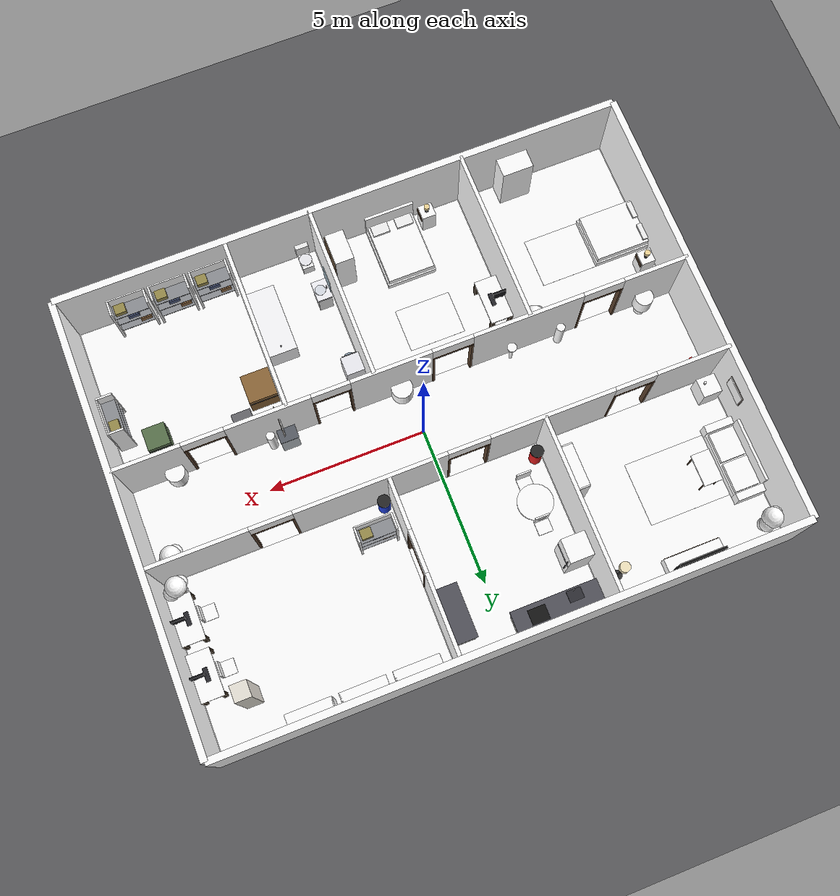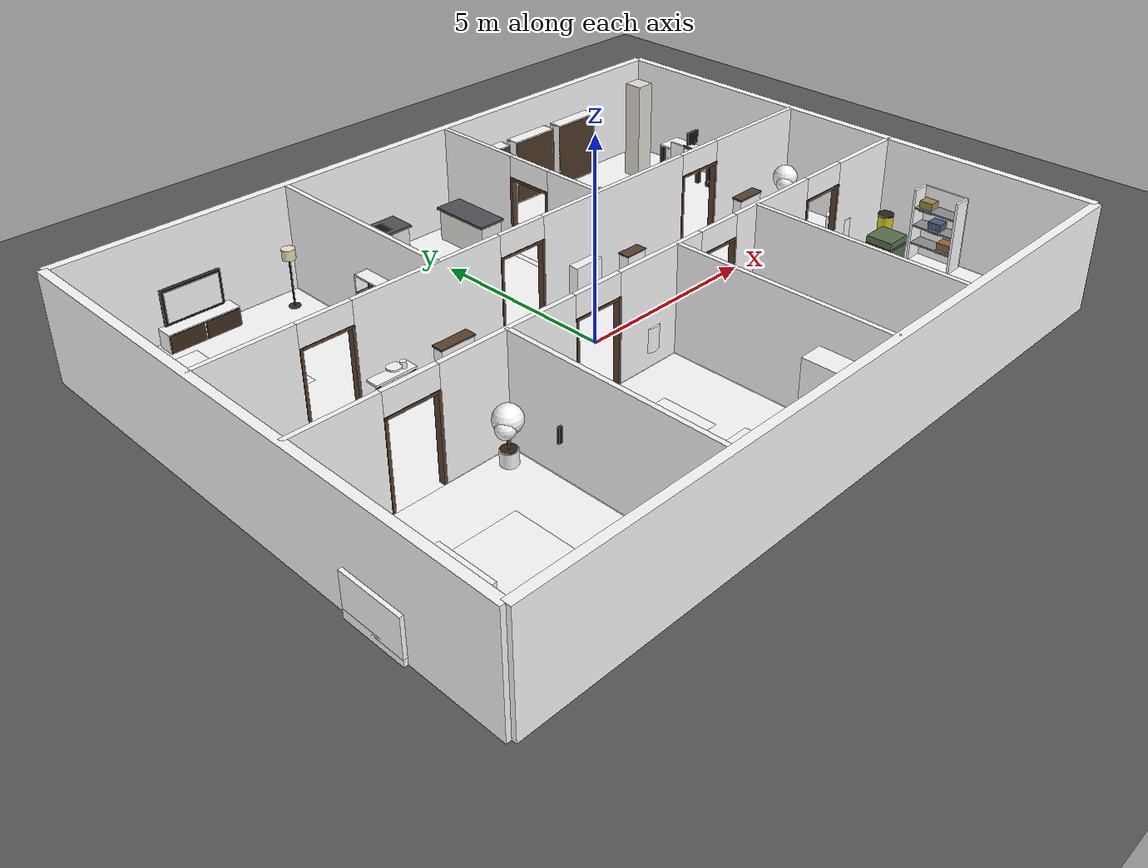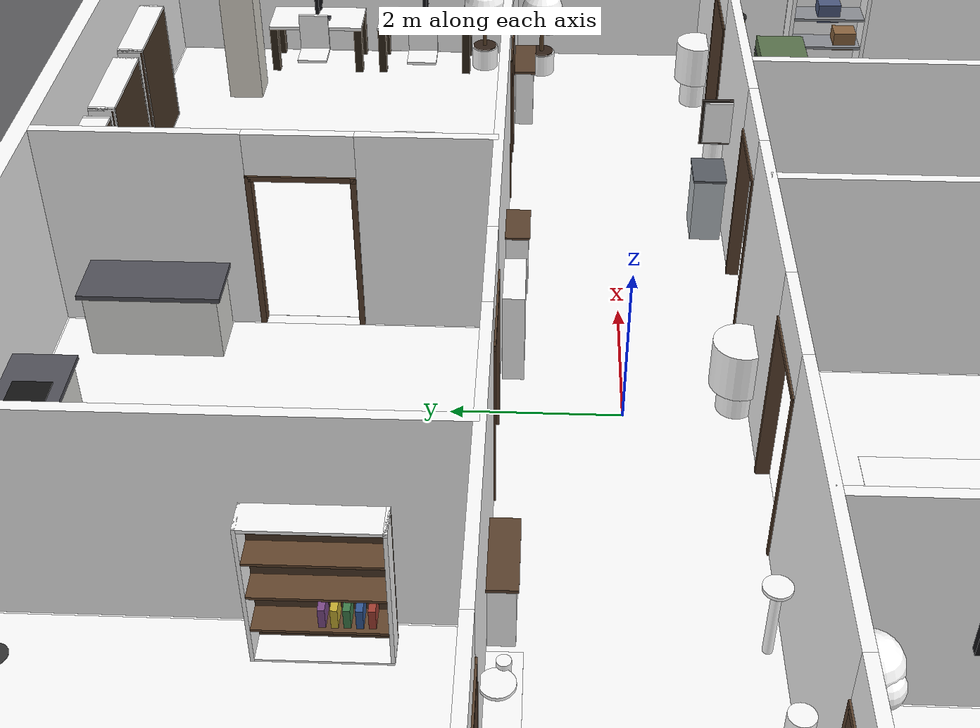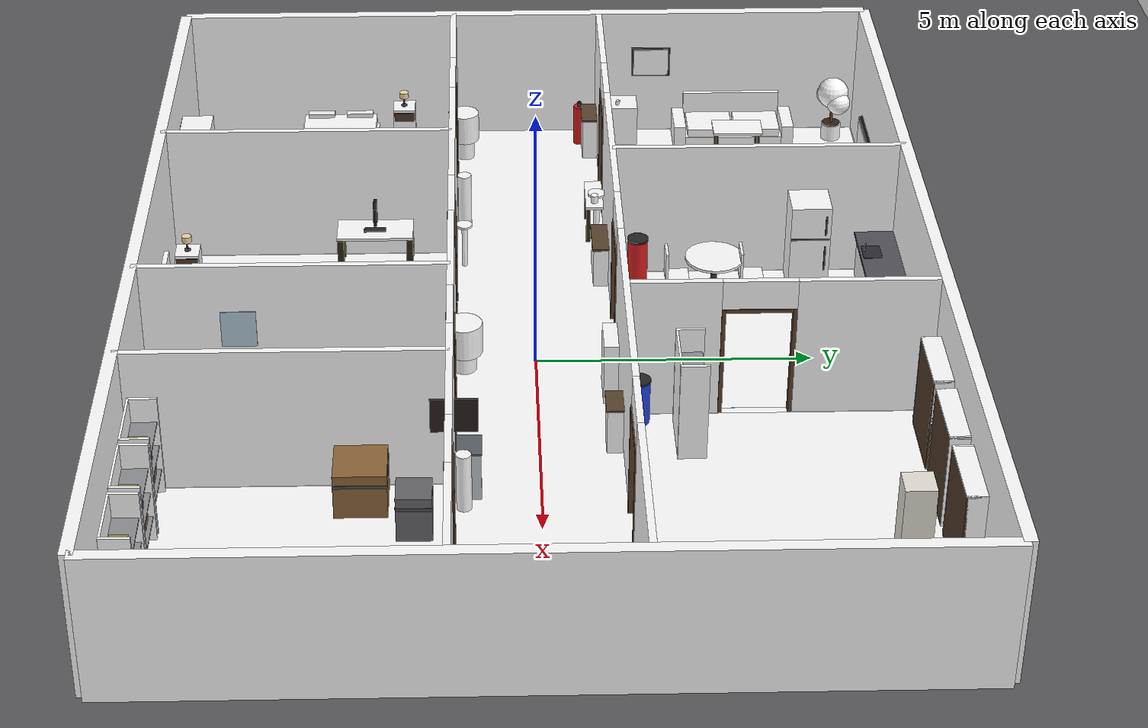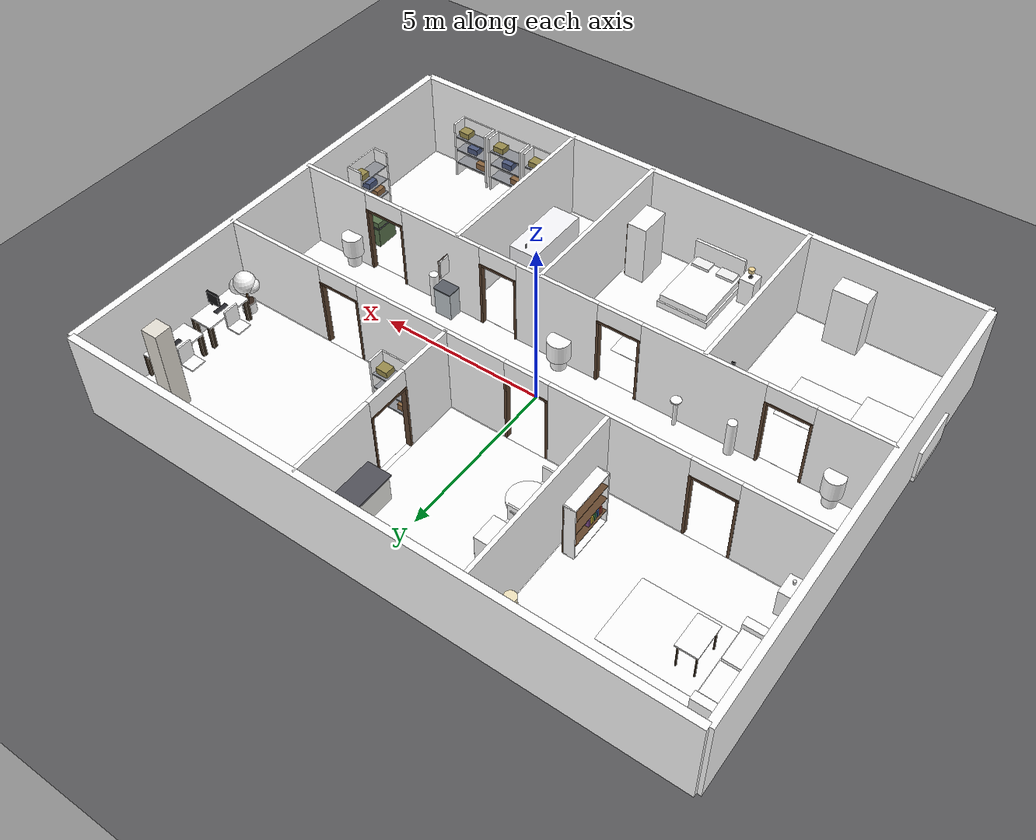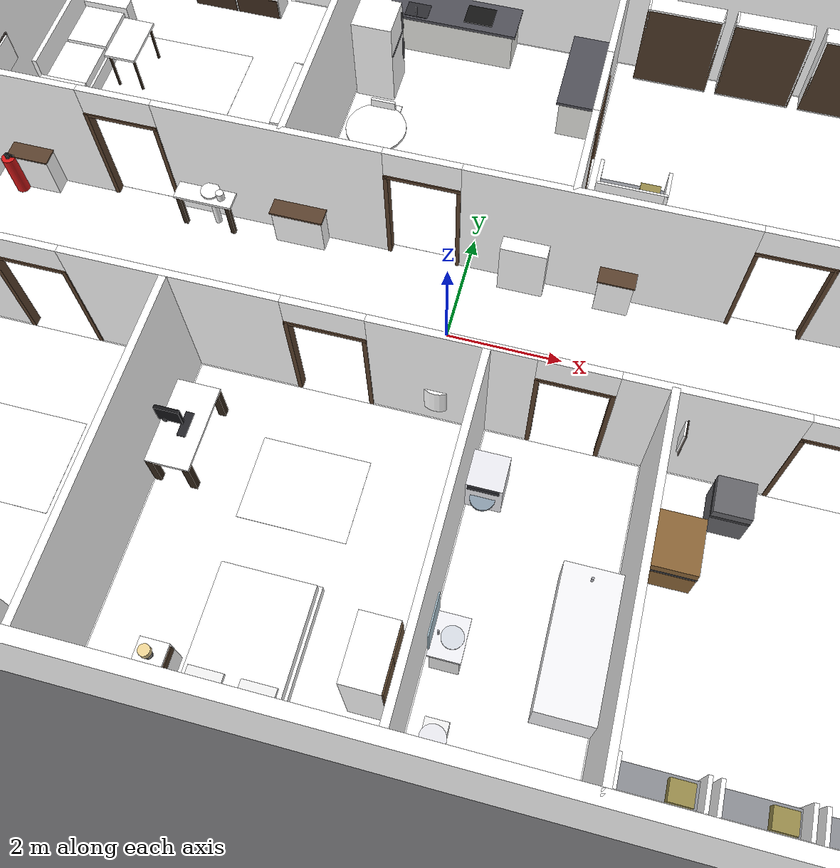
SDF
<sdf version="1.9">
 <world name="dan_house">
  <physics name="1ms" type="ignored">
   <max_step_size>0.001</max_step_size>
   <real_time_factor>1.0</real_time_factor>
  </physics>
  <plugin filename="gz-sim-physics-system" name="gz::sim::systems::Physics"/>
  <plugin filename="gz-sim-user-commands-system" name="gz::sim::systems::UserCommands"/>
  <plugin filename="gz-sim-scene-broadcaster-system" name="gz::sim::systems::SceneBroadcaster"/>
  <plugin filename="gz-sim-sensors-system" name="gz::sim::systems::Sensors">
   <render_engine>ogre2</render_engine>
  </plugin>
  <plugin filename="gz-sim-imu-system" name="gz::sim::systems::Imu"/>
  <scene><ambient>0.32 0.32 0.32 1</ambient></scene>
  <light type="directional" name="sun">
   <pose>0 0 10 0 0 0</pose>
   <diffuse>0.8 0.8 0.8 1</diffuse>
   <specular>0.2 0.2 0.2 1</specular>
   <direction>-0.5 0.1 -0.9</direction>
  </light>
  <light type="point" name="light_living">
   <cast_shadows>false</cast_shadows>
   <pose>-6.045 4.225 2.5500000000000003 0 0 0</pose>
   <diffuse>1.0 0.94 0.85 1</diffuse>
   <attenuation>
    <range>15</range>
    <constant>0.4</constant>
    <linear>0.3</linear>
    <quadratic>0.02</quadratic>
   </attenuation>
  </light>
  <light type="point" name="light_kitchen">
   <cast_shadows>false</cast_shadows>
   <pose>-0.74 4.225 2.5500000000000003 0 0 0</pose>
   <diffuse>1.0 1.0 1.0 1</diffuse>
   <attenuation>
    <range>15</range>
    <constant>0.4</constant>
    <linear>0.3</linear>
    <quadratic>0.02</quadratic>
   </attenuation>
  </light>
  <light type="point" name="light_study">
   <cast_shadows>false</cast_shadows>
   <pose>5.305000000000001 4.225 2.5500000000000003 0 0 0</pose>
   <diffuse>1.0 1.0 1.0 1</diffuse>
   <attenuation>
    <range>15</range>
    <constant>0.4</constant>
    <linear>0.3</linear>
    <quadratic>0.02</quadratic>
   </attenuation>
  </light>
  <light type="point" name="light_bed1">
   <cast_shadows>false</cast_shadows>
   <pose>-6.445 -4.225 2.5500000000000003 0 0 0</pose>
   <diffuse>1.0 0.94 0.85 1</diffuse>
   <attenuation>
    <range>15</range>
    <constant>0.4</constant>
    <linear>0.3</linear>
    <quadratic>0.02</quadratic>
   </attenuation>
  </light>
  <light type="point" name="light_bed2">
   <cast_shadows>false</cast_shadows>
   <pose>-1.49 -4.225 2.5500000000000003 0 0 0</pose>
   <diffuse>1.0 0.94 0.85 1</diffuse>
   <attenuation>
    <range>15</range>
    <constant>0.4</constant>
    <linear>0.3</linear>
    <quadratic>0.02</quadratic>
   </attenuation>
  </light>
  <light type="point" name="light_bath">
   <cast_shadows>false</cast_shadows>
   <pose>2.31 -4.225 2.5500000000000003 0 0 0</pose>
   <diffuse>1.0 1.0 1.0 1</diffuse>
   <attenuation>
    <range>15</range>
    <constant>0.4</constant>
    <linear>0.3</linear>
    <quadratic>0.02</quadratic>
   </attenuation>
  </light>
  <light type="point" name="light_store">
   <cast_shadows>false</cast_shadows>
   <pose>6.305000000000001 -4.225 2.5500000000000003 0 0 0</pose>
   <diffuse>1.0 1.0 1.0 1</diffuse>
   <attenuation>
    <range>15</range>
    <constant>0.4</constant>
    <linear>0.3</linear>
    <quadratic>0.02</quadratic>
   </attenuation>
  </light>
  <light type="point" name="light_corridor_0">
   <cast_shadows>false</cast_shadows>
   <pose>-7.5 0 2.5500000000000003 0 0 0</pose>
   <diffuse>1.0 0.98 0.92 1</diffuse>
   <attenuation>
    <range>11</range>
    <constant>0.5</constant>
    <linear>0.35</linear>
    <quadratic>0.04</quadratic>
   </attenuation>
  </light>
  <light type="point" name="light_corridor_1">
   <cast_shadows>false</cast_shadows>
   <pose>-3.5 0 2.5500000000000003 0 0 0</pose>
   <diffuse>1.0 0.98 0.92 1</diffuse>
   <attenuation>
    <range>11</range>
    <constant>0.5</constant>
    <linear>0.35</linear>
    <quadratic>0.04</quadratic>
   </attenuation>
  </light>
  <light type="point" name="light_corridor_2">
   <cast_shadows>false</cast_shadows>
   <pose>0.0 0 2.5500000000000003 0 0 0</pose>
   <diffuse>1.0 0.98 0.92 1</diffuse>
   <attenuation>
    <range>11</range>
    <constant>0.5</constant>
    <linear>0.35</linear>
    <quadratic>0.04</quadratic>
   </attenuation>
  </light>
  <light type="point" name="light_corridor_3">
   <cast_shadows>false</cast_shadows>
   <pose>3.5 0 2.5500000000000003 0 0 0</pose>
   <diffuse>1.0 0.98 0.92 1</diffuse>
   <attenuation>
    <range>11</range>
    <constant>0.5</constant>
    <linear>0.35</linear>
    <quadratic>0.04</quadratic>
   </attenuation>
  </light>
  <light type="point" name="light_corridor_4">
   <cast_shadows>false</cast_shadows>
   <pose>7.5 0 2.5500000000000003 0 0 0</pose>
   <diffuse>1.0 0.98 0.92 1</diffuse>
   <attenuation>
    <range>11</range>
    <constant>0.5</constant>
    <linear>0.35</linear>
    <quadratic>0.04</quadratic>
   </attenuation>
  </light>
  <model name="ground_plane">
   <static>true</static>
   <link name="link">
    <collision name="c"><geometry><plane><normal>0 0 1</normal><size>90 90</size></plane></geometry></collision>
    <visual name="v">
     <geometry><plane><normal>0 0 1</normal><size>90 90</size></plane></geometry>
     <material><diffuse>0.35 0.35 0.36 1</diffuse></material>
    </visual>
   </link>
  </model>
  <model name="floor_main">
   <static>true</static>
   <link name="link">
    <collision name="c">
     <pose>0 0 0.006 0 0 0</pose>
     <geometry><box><size>17.780 13.780 0.012</size></box></geometry>
    </collision>
    <visual name="v">
     <pose>0 0 0.006 0 0 0</pose>
     <geometry><box><size>17.780 13.780 0.012</size></box></geometry>
     <material>
      <diffuse>1 1 1 1</diffuse>
      <pbr>
       <metal>
        <albedo_map>textures/wood_floor.jpg</albedo_map>
        <metalness>0.0</metalness>
        <roughness>0.85</roughness>
       </metal>
      </pbr>
     </material>
    </visual>
   </link>
  </model>
  <model name="floor_tex_living">
   <static>true</static>
   <link name="link">
    <visual name="v">
     <pose>-6.045 4.225 0.0125 0 0 0</pose>
     <geometry><box><size>5.650 5.290 0.001</size></box></geometry>
     <material>
      <diffuse>1 1 1 1</diffuse>
      <pbr>
       <metal>
        <albedo_map>textures/wood_floor.jpg</albedo_map>
        <metalness>0.0</metalness>
        <roughness>0.85</roughness>
       </metal>
      </pbr>
     </material>
    </visual>
   </link>
  </model>
  <model name="floor_tex_kitchen">
   <static>true</static>
   <link name="link">
    <visual name="v">
     <pose>-0.74 4.225 0.0125 0 0 0</pose>
     <geometry><box><size>4.640 5.290 0.001</size></box></geometry>
     <material>
      <diffuse>1 1 1 1</diffuse>
      <pbr>
       <metal><albedo_map>textures/tile.jpg</albedo_map><metalness>0.0</metalness><roughness>0.85</roughness></metal>
      </pbr>
     </material>
    </visual>
   </link>
  </model>
  <model name="floor_tex_study">
   <static>true</static>
   <link name="link">
    <visual name="v">
     <pose>5.305000000000001 4.225 0.0125 0 0 0</pose>
     <geometry><box><size>7.130 5.290 0.001</size></box></geometry>
     <material>
      <diffuse>1 1 1 1</diffuse>
      <pbr>
       <metal>
        <albedo_map>textures/wood_dark.jpg</albedo_map>
        <metalness>0.0</metalness>
        <roughness>0.85</roughness>
       </metal>
      </pbr>
     </material>
    </visual>
   </link>
  </model>
  <model name="floor_tex_bed1">
   <static>true</static>
   <link name="link">
    <visual name="v">
     <pose>-6.445 -4.225 0.0125 0 0 0</pose>
     <geometry><box><size>4.850 5.290 0.001</size></box></geometry>
     <material>
      <diffuse>1 1 1 1</diffuse>
      <pbr>
       <metal>
        <albedo_map>textures/carpet.jpg</albedo_map>
        <metalness>0.0</metalness>
        <roughness>0.85</roughness>
       </metal>
      </pbr>
     </material>
    </visual>
   </link>
  </model>
  <model name="floor_tex_bed2">
   <static>true</static>
   <link name="link">
    <visual name="v">
     <pose>-1.49 -4.225 0.0125 0 0 0</pose>
     <geometry><box><size>4.740 5.290 0.001</size></box></geometry>
     <material>
      <diffuse>1 1 1 1</diffuse>
      <pbr>
       <metal>
        <albedo_map>textures/carpet.jpg</albedo_map>
        <metalness>0.0</metalness>
        <roughness>0.85</roughness>
       </metal>
      </pbr>
     </material>
    </visual>
   </link>
  </model>
  <model name="floor_tex_bath">
   <static>true</static>
   <link name="link">
    <visual name="v">
     <pose>2.31 -4.225 0.0125 0 0 0</pose>
     <geometry><box><size>2.540 5.290 0.001</size></box></geometry>
     <material>
      <diffuse>1 1 1 1</diffuse>
      <pbr>
       <metal><albedo_map>textures/tile.jpg</albedo_map><metalness>0.0</metalness><roughness>0.85</roughness></metal>
      </pbr>
     </material>
    </visual>
   </link>
  </model>
  <model name="floor_tex_store">
   <static>true</static>
   <link name="link">
    <visual name="v">
     <pose>6.305000000000001 -4.225 0.0125 0 0 0</pose>
     <geometry><box><size>5.130 5.290 0.001</size></box></geometry>
     <material>
      <diffuse>1 1 1 1</diffuse>
      <pbr>
       <metal>
        <albedo_map>textures/wood_dark.jpg</albedo_map>
        <metalness>0.0</metalness>
        <roughness>0.85</roughness>
       </metal>
      </pbr>
     </material>
    </visual>
   </link>
  </model>
  <model name="wall_south_0">
   <pose>0.000 -7.0 1.35 0 0 0</pose>
   <static>true</static>
   <link name="link">
    <collision name="c"><geometry><box><size>18.000 0.22 2.7</size></box></geometry></collision>
    <visual name="v">
     <geometry><box><size>18.000 0.22 2.7</size></box></geometry>
     <material>
      <diffuse>1 1 1 1</diffuse>
      <pbr>
       <metal>
        <albedo_map>textures/wallpaper.jpg</albedo_map>
        <metalness>0.0</metalness>
        <roughness>0.85</roughness>
       </metal>
      </pbr>
     </material>
    </visual>
   </link>
  </model>
  <model name="wall_north_0">
   <pose>0.000 7.0 1.35 0 0 0</pose>
   <static>true</static>
   <link name="link">
    <collision name="c"><geometry><box><size>18.000 0.22 2.7</size></box></geometry></collision>
    <visual name="v">
     <geometry><box><size>18.000 0.22 2.7</size></box></geometry>
     <material>
      <diffuse>1 1 1 1</diffuse>
      <pbr>
       <metal>
        <albedo_map>textures/wallpaper.jpg</albedo_map>
        <metalness>0.0</metalness>
        <roughness>0.85</roughness>
       </metal>
      </pbr>
     </material>
    </visual>
   </link>
  </model>
  <model name="wall_west_0">
   <pose>-9.0 0.000 1.35 0 0 0</pose>
   <static>true</static>
   <link name="link">
    <collision name="c"><geometry><box><size>0.22 14.000 2.7</size></box></geometry></collision>
    <visual name="v">
     <geometry><box><size>0.22 14.000 2.7</size></box></geometry>
     <material>
      <diffuse>1 1 1 1</diffuse>
      <pbr>
       <metal>
        <albedo_map>textures/wallpaper.jpg</albedo_map>
        <metalness>0.0</metalness>
        <roughness>0.85</roughness>
       </metal>
      </pbr>
     </material>
    </visual>
   </link>
  </model>
  <model name="wall_east_0">
   <pose>9.0 0.000 1.35 0 0 0</pose>
   <static>true</static>
   <link name="link">
    <collision name="c"><geometry><box><size>0.22 14.000 2.7</size></box></geometry></collision>
    <visual name="v">
     <geometry><box><size>0.22 14.000 2.7</size></box></geometry>
     <material>
      <diffuse>1 1 1 1</diffuse>
      <pbr>
       <metal>
        <albedo_map>textures/wallpaper.jpg</albedo_map>
        <metalness>0.0</metalness>
        <roughness>0.85</roughness>
       </metal>
      </pbr>
     </material>
    </visual>
   </link>
  </model>
  <model name="wall_corr_north_0">
   <pose>-7.825 1.5 1.35 0 0 0</pose>
   <static>true</static>
   <link name="link">
    <collision name="c"><geometry><box><size>2.350 0.12 2.7</size></box></geometry></collision>
    <visual name="v">
     <geometry><box><size>2.350 0.12 2.7</size></box></geometry>
     <material>
      <diffuse>1 1 1 1</diffuse>
      <pbr>
       <metal>
        <albedo_map>textures/wallpaper.jpg</albedo_map>
        <metalness>0.0</metalness>
        <roughness>0.85</roughness>
       </metal>
      </pbr>
     </material>
    </visual>
   </link>
  </model>
  <model name="wall_corr_north_1">
   <pose>-3.400 1.5 1.35 0 0 0</pose>
   <static>true</static>
   <link name="link">
    <collision name="c"><geometry><box><size>3.900 0.12 2.7</size></box></geometry></collision>
    <visual name="v">
     <geometry><box><size>3.900 0.12 2.7</size></box></geometry>
     <material>
      <diffuse>1 1 1 1</diffuse>
      <pbr>
       <metal>
        <albedo_map>textures/wallpaper.jpg</albedo_map>
        <metalness>0.0</metalness>
        <roughness>0.85</roughness>
       </metal>
      </pbr>
     </material>
    </visual>
   </link>
  </model>
  <model name="wall_corr_north_2">
   <pose>2.200 1.5 1.35 0 0 0</pose>
   <static>true</static>
   <link name="link">
    <collision name="c"><geometry><box><size>4.700 0.12 2.7</size></box></geometry></collision>
    <visual name="v">
     <geometry><box><size>4.700 0.12 2.7</size></box></geometry>
     <material>
      <diffuse>1 1 1 1</diffuse>
      <pbr>
       <metal>
        <albedo_map>textures/wallpaper.jpg</albedo_map>
        <metalness>0.0</metalness>
        <roughness>0.85</roughness>
       </metal>
      </pbr>
     </material>
    </visual>
   </link>
  </model>
  <model name="wall_corr_north_3">
   <pose>7.425 1.5 1.35 0 0 0</pose>
   <static>true</static>
   <link name="link">
    <collision name="c"><geometry><box><size>3.150 0.12 2.7</size></box></geometry></collision>
    <visual name="v">
     <geometry><box><size>3.150 0.12 2.7</size></box></geometry>
     <material>
      <diffuse>1 1 1 1</diffuse>
      <pbr>
       <metal>
        <albedo_map>textures/wallpaper.jpg</albedo_map>
        <metalness>0.0</metalness>
        <roughness>0.85</roughness>
       </metal>
      </pbr>
     </material>
    </visual>
   </link>
  </model>
  <model name="wall_corr_north_door_-6.0_p0">
   <pose>-6.615 1.5 1.075 0 0 0</pose>
   <static>true</static>
   <link name="link">
    <visual name="v">
     <geometry><box><size>0.07 0.160 2.15</size></box></geometry>
     <material><diffuse>0.36 0.26 0.18 1</diffuse></material>
    </visual>
   </link>
  </model>
  <model name="wall_corr_north_door_-6.0_p1">
   <pose>-5.385 1.5 1.075 0 0 0</pose>
   <static>true</static>
   <link name="link">
    <visual name="v">
     <geometry><box><size>0.07 0.160 2.15</size></box></geometry>
     <material><diffuse>0.36 0.26 0.18 1</diffuse></material>
    </visual>
   </link>
  </model>
  <model name="wall_corr_north_door_-6.0_top">
   <pose>-6.0 1.5 2.1149999999999998 0 0 0</pose>
   <static>true</static>
   <link name="link">
    <visual name="v">
     <geometry><box><size>1.3 0.160 0.07</size></box></geometry>
     <material><diffuse>0.36 0.26 0.18 1</diffuse></material>
    </visual>
   </link>
  </model>
  <model name="wall_corr_north_door_-6.0_lintel">
   <pose>-6.0 1.5 2.4000000000000004 0 0 0</pose>
   <static>true</static>
   <link name="link">
    <visual name="v">
     <geometry><box><size>1.3 0.12 0.600</size></box></geometry>
     <material>
      <diffuse>1 1 1 1</diffuse>
      <pbr>
       <metal>
        <albedo_map>textures/wallpaper.jpg</albedo_map>
        <metalness>0.0</metalness>
        <roughness>0.85</roughness>
       </metal>
      </pbr>
     </material>
    </visual>
   </link>
  </model>
  <model name="wall_corr_north_door_-0.8_p0">
   <pose>-1.415 1.5 1.075 0 0 0</pose>
   <static>true</static>
   <link name="link">
    <visual name="v">
     <geometry><box><size>0.07 0.160 2.15</size></box></geometry>
     <material><diffuse>0.36 0.26 0.18 1</diffuse></material>
    </visual>
   </link>
  </model>
  <model name="wall_corr_north_door_-0.8_p1">
   <pose>-0.18500000000000005 1.5 1.075 0 0 0</pose>
   <static>true</static>
   <link name="link">
    <visual name="v">
     <geometry><box><size>0.07 0.160 2.15</size></box></geometry>
     <material><diffuse>0.36 0.26 0.18 1</diffuse></material>
    </visual>
   </link>
  </model>
  <model name="wall_corr_north_door_-0.8_top">
   <pose>-0.8 1.5 2.1149999999999998 0 0 0</pose>
   <static>true</static>
   <link name="link">
    <visual name="v">
     <geometry><box><size>1.3 0.160 0.07</size></box></geometry>
     <material><diffuse>0.36 0.26 0.18 1</diffuse></material>
    </visual>
   </link>
  </model>
  <model name="wall_corr_north_door_-0.8_lintel">
   <pose>-0.8 1.5 2.4000000000000004 0 0 0</pose>
   <static>true</static>
   <link name="link">
    <visual name="v">
     <geometry><box><size>1.3 0.12 0.600</size></box></geometry>
     <material>
      <diffuse>1 1 1 1</diffuse>
      <pbr>
       <metal>
        <albedo_map>textures/wallpaper.jpg</albedo_map>
        <metalness>0.0</metalness>
        <roughness>0.85</roughness>
       </metal>
      </pbr>
     </material>
    </visual>
   </link>
  </model>
  <model name="wall_corr_north_door_5.2_p0">
   <pose>4.585 1.5 1.075 0 0 0</pose>
   <static>true</static>
   <link name="link">
    <visual name="v">
     <geometry><box><size>0.07 0.160 2.15</size></box></geometry>
     <material><diffuse>0.36 0.26 0.18 1</diffuse></material>
    </visual>
   </link>
  </model>
  <model name="wall_corr_north_door_5.2_p1">
   <pose>5.815 1.5 1.075 0 0 0</pose>
   <static>true</static>
   <link name="link">
    <visual name="v">
     <geometry><box><size>0.07 0.160 2.15</size></box></geometry>
     <material><diffuse>0.36 0.26 0.18 1</diffuse></material>
    </visual>
   </link>
  </model>
  <model name="wall_corr_north_door_5.2_top">
   <pose>5.2 1.5 2.1149999999999998 0 0 0</pose>
   <static>true</static>
   <link name="link">
    <visual name="v">
     <geometry><box><size>1.3 0.160 0.07</size></box></geometry>
     <material><diffuse>0.36 0.26 0.18 1</diffuse></material>
    </visual>
   </link>
  </model>
  <model name="wall_corr_north_door_5.2_lintel">
   <pose>5.2 1.5 2.4000000000000004 0 0 0</pose>
   <static>true</static>
   <link name="link">
    <visual name="v">
     <geometry><box><size>1.3 0.12 0.600</size></box></geometry>
     <material>
      <diffuse>1 1 1 1</diffuse>
      <pbr>
       <metal>
        <albedo_map>textures/wallpaper.jpg</albedo_map>
        <metalness>0.0</metalness>
        <roughness>0.85</roughness>
       </metal>
      </pbr>
     </material>
    </visual>
   </link>
  </model>
  <model name="wall_corr_south_0">
   <pose>-7.975 -1.5 1.35 0 0 0</pose>
   <static>true</static>
   <link name="link">
    <collision name="c"><geometry><box><size>2.050 0.12 2.7</size></box></geometry></collision>
    <visual name="v">
     <geometry><box><size>2.050 0.12 2.7</size></box></geometry>
     <material>
      <diffuse>1 1 1 1</diffuse>
      <pbr>
       <metal>
        <albedo_map>textures/wallpaper.jpg</albedo_map>
        <metalness>0.0</metalness>
        <roughness>0.85</roughness>
       </metal>
      </pbr>
     </material>
    </visual>
   </link>
  </model>
  <model name="wall_corr_south_1">
   <pose>-3.900 -1.5 1.35 0 0 0</pose>
   <static>true</static>
   <link name="link">
    <collision name="c"><geometry><box><size>3.500 0.12 2.7</size></box></geometry></collision>
    <visual name="v">
     <geometry><box><size>3.500 0.12 2.7</size></box></geometry>
     <material>
      <diffuse>1 1 1 1</diffuse>
      <pbr>
       <metal>
        <albedo_map>textures/wallpaper.jpg</albedo_map>
        <metalness>0.0</metalness>
        <roughness>0.85</roughness>
       </metal>
      </pbr>
     </material>
    </visual>
   </link>
  </model>
  <model name="wall_corr_south_2">
   <pose>0.425 -1.5 1.35 0 0 0</pose>
   <static>true</static>
   <link name="link">
    <collision name="c"><geometry><box><size>2.550 0.12 2.7</size></box></geometry></collision>
    <visual name="v">
     <geometry><box><size>2.550 0.12 2.7</size></box></geometry>
     <material>
      <diffuse>1 1 1 1</diffuse>
      <pbr>
       <metal>
        <albedo_map>textures/wallpaper.jpg</albedo_map>
        <metalness>0.0</metalness>
        <roughness>0.85</roughness>
       </metal>
      </pbr>
     </material>
    </visual>
   </link>
  </model>
  <model name="wall_corr_south_3">
   <pose>4.225 -1.5 1.35 0 0 0</pose>
   <static>true</static>
   <link name="link">
    <collision name="c"><geometry><box><size>2.650 0.12 2.7</size></box></geometry></collision>
    <visual name="v">
     <geometry><box><size>2.650 0.12 2.7</size></box></geometry>
     <material>
      <diffuse>1 1 1 1</diffuse>
      <pbr>
       <metal>
        <albedo_map>textures/wallpaper.jpg</albedo_map>
        <metalness>0.0</metalness>
        <roughness>0.85</roughness>
       </metal>
      </pbr>
     </material>
    </visual>
   </link>
  </model>
  <model name="wall_corr_south_4">
   <pose>7.925 -1.5 1.35 0 0 0</pose>
   <static>true</static>
   <link name="link">
    <collision name="c"><geometry><box><size>2.150 0.12 2.7</size></box></geometry></collision>
    <visual name="v">
     <geometry><box><size>2.150 0.12 2.7</size></box></geometry>
     <material>
      <diffuse>1 1 1 1</diffuse>
      <pbr>
       <metal>
        <albedo_map>textures/wallpaper.jpg</albedo_map>
        <metalness>0.0</metalness>
        <roughness>0.85</roughness>
       </metal>
      </pbr>
     </material>
    </visual>
   </link>
  </model>
  <model name="wall_corr_south_door_-6.3_p0">
   <pose>-6.915 -1.5 1.075 0 0 0</pose>
   <static>true</static>
   <link name="link">
    <visual name="v">
     <geometry><box><size>0.07 0.160 2.15</size></box></geometry>
     <material><diffuse>0.36 0.26 0.18 1</diffuse></material>
    </visual>
   </link>
  </model>
  <model name="wall_corr_south_door_-6.3_p1">
   <pose>-5.685 -1.5 1.075 0 0 0</pose>
   <static>true</static>
   <link name="link">
    <visual name="v">
     <geometry><box><size>0.07 0.160 2.15</size></box></geometry>
     <material><diffuse>0.36 0.26 0.18 1</diffuse></material>
    </visual>
   </link>
  </model>
  <model name="wall_corr_south_door_-6.3_top">
   <pose>-6.3 -1.5 2.1149999999999998 0 0 0</pose>
   <static>true</static>
   <link name="link">
    <visual name="v">
     <geometry><box><size>1.3 0.160 0.07</size></box></geometry>
     <material><diffuse>0.36 0.26 0.18 1</diffuse></material>
    </visual>
   </link>
  </model>
  <model name="wall_corr_south_door_-6.3_lintel">
   <pose>-6.3 -1.5 2.4000000000000004 0 0 0</pose>
   <static>true</static>
   <link name="link">
    <visual name="v">
     <geometry><box><size>1.3 0.12 0.600</size></box></geometry>
     <material>
      <diffuse>1 1 1 1</diffuse>
      <pbr>
       <metal>
        <albedo_map>textures/wallpaper.jpg</albedo_map>
        <metalness>0.0</metalness>
        <roughness>0.85</roughness>
       </metal>
      </pbr>
     </material>
    </visual>
   </link>
  </model>
  <model name="wall_corr_south_door_-1.5_p0">
   <pose>-2.115 -1.5 1.075 0 0 0</pose>
   <static>true</static>
   <link name="link">
    <visual name="v">
     <geometry><box><size>0.07 0.160 2.15</size></box></geometry>
     <material><diffuse>0.36 0.26 0.18 1</diffuse></material>
    </visual>
   </link>
  </model>
  <model name="wall_corr_south_door_-1.5_p1">
   <pose>-0.885 -1.5 1.075 0 0 0</pose>
   <static>true</static>
   <link name="link">
    <visual name="v">
     <geometry><box><size>0.07 0.160 2.15</size></box></geometry>
     <material><diffuse>0.36 0.26 0.18 1</diffuse></material>
    </visual>
   </link>
  </model>
  <model name="wall_corr_south_door_-1.5_top">
   <pose>-1.5 -1.5 2.1149999999999998 0 0 0</pose>
   <static>true</static>
   <link name="link">
    <visual name="v">
     <geometry><box><size>1.3 0.160 0.07</size></box></geometry>
     <material><diffuse>0.36 0.26 0.18 1</diffuse></material>
    </visual>
   </link>
  </model>
  <model name="wall_corr_south_door_-1.5_lintel">
   <pose>-1.5 -1.5 2.4000000000000004 0 0 0</pose>
   <static>true</static>
   <link name="link">
    <visual name="v">
     <geometry><box><size>1.3 0.12 0.600</size></box></geometry>
     <material>
      <diffuse>1 1 1 1</diffuse>
      <pbr>
       <metal>
        <albedo_map>textures/wallpaper.jpg</albedo_map>
        <metalness>0.0</metalness>
        <roughness>0.85</roughness>
       </metal>
      </pbr>
     </material>
    </visual>
   </link>
  </model>
  <model name="wall_corr_south_door_2.3_p0">
   <pose>1.7349999999999999 -1.5 1.075 0 0 0</pose>
   <static>true</static>
   <link name="link">
    <visual name="v">
     <geometry><box><size>0.07 0.160 2.15</size></box></geometry>
     <material><diffuse>0.36 0.26 0.18 1</diffuse></material>
    </visual>
   </link>
  </model>
  <model name="wall_corr_south_door_2.3_p1">
   <pose>2.8649999999999998 -1.5 1.075 0 0 0</pose>
   <static>true</static>
   <link name="link">
    <visual name="v">
     <geometry><box><size>0.07 0.160 2.15</size></box></geometry>
     <material><diffuse>0.36 0.26 0.18 1</diffuse></material>
    </visual>
   </link>
  </model>
  <model name="wall_corr_south_door_2.3_top">
   <pose>2.3 -1.5 2.1149999999999998 0 0 0</pose>
   <static>true</static>
   <link name="link">
    <visual name="v">
     <geometry><box><size>1.2 0.160 0.07</size></box></geometry>
     <material><diffuse>0.36 0.26 0.18 1</diffuse></material>
    </visual>
   </link>
  </model>
  <model name="wall_corr_south_door_2.3_lintel">
   <pose>2.3 -1.5 2.4000000000000004 0 0 0</pose>
   <static>true</static>
   <link name="link">
    <visual name="v">
     <geometry><box><size>1.2 0.12 0.600</size></box></geometry>
     <material>
      <diffuse>1 1 1 1</diffuse>
      <pbr>
       <metal>
        <albedo_map>textures/wallpaper.jpg</albedo_map>
        <metalness>0.0</metalness>
        <roughness>0.85</roughness>
       </metal>
      </pbr>
     </material>
    </visual>
   </link>
  </model>
  <model name="wall_corr_south_door_6.2_p0">
   <pose>5.585 -1.5 1.075 0 0 0</pose>
   <static>true</static>
   <link name="link">
    <visual name="v">
     <geometry><box><size>0.07 0.160 2.15</size></box></geometry>
     <material><diffuse>0.36 0.26 0.18 1</diffuse></material>
    </visual>
   </link>
  </model>
  <model name="wall_corr_south_door_6.2_p1">
   <pose>6.815 -1.5 1.075 0 0 0</pose>
   <static>true</static>
   <link name="link">
    <visual name="v">
     <geometry><box><size>0.07 0.160 2.15</size></box></geometry>
     <material><diffuse>0.36 0.26 0.18 1</diffuse></material>
    </visual>
   </link>
  </model>
  <model name="wall_corr_south_door_6.2_top">
   <pose>6.2 -1.5 2.1149999999999998 0 0 0</pose>
   <static>true</static>
   <link name="link">
    <visual name="v">
     <geometry><box><size>1.3 0.160 0.07</size></box></geometry>
     <material><diffuse>0.36 0.26 0.18 1</diffuse></material>
    </visual>
   </link>
  </model>
  <model name="wall_corr_south_door_6.2_lintel">
   <pose>6.2 -1.5 2.4000000000000004 0 0 0</pose>
   <static>true</static>
   <link name="link">
    <visual name="v">
     <geometry><box><size>1.3 0.12 0.600</size></box></geometry>
     <material>
      <diffuse>1 1 1 1</diffuse>
      <pbr>
       <metal>
        <albedo_map>textures/wallpaper.jpg</albedo_map>
        <metalness>0.0</metalness>
        <roughness>0.85</roughness>
       </metal>
      </pbr>
     </material>
    </visual>
   </link>
  </model>
  <model name="wall_living_kitchen_0">
   <pose>-3.14 4.250 1.35 0 0 0</pose>
   <static>true</static>
   <link name="link">
    <collision name="c"><geometry><box><size>0.12 5.500 2.7</size></box></geometry></collision>
    <visual name="v">
     <geometry><box><size>0.12 5.500 2.7</size></box></geometry>
     <material>
      <diffuse>1 1 1 1</diffuse>
      <pbr>
       <metal>
        <albedo_map>textures/wallpaper.jpg</albedo_map>
        <metalness>0.0</metalness>
        <roughness>0.85</roughness>
       </metal>
      </pbr>
     </material>
    </visual>
   </link>
  </model>
  <model name="wall_kitchen_study_0">
   <pose>1.66 2.325 1.35 0 0 0</pose>
   <static>true</static>
   <link name="link">
    <collision name="c"><geometry><box><size>0.12 1.650 2.7</size></box></geometry></collision>
    <visual name="v">
     <geometry><box><size>0.12 1.650 2.7</size></box></geometry>
     <material>
      <diffuse>1 1 1 1</diffuse>
      <pbr>
       <metal>
        <albedo_map>textures/wallpaper.jpg</albedo_map>
        <metalness>0.0</metalness>
        <roughness>0.85</roughness>
       </metal>
      </pbr>
     </material>
    </visual>
   </link>
  </model>
  <model name="wall_kitchen_study_1">
   <pose>1.66 5.725 1.35 0 0 0</pose>
   <static>true</static>
   <link name="link">
    <collision name="c"><geometry><box><size>0.12 2.550 2.7</size></box></geometry></collision>
    <visual name="v">
     <geometry><box><size>0.12 2.550 2.7</size></box></geometry>
     <material>
      <diffuse>1 1 1 1</diffuse>
      <pbr>
       <metal>
        <albedo_map>textures/wallpaper.jpg</albedo_map>
        <metalness>0.0</metalness>
        <roughness>0.85</roughness>
       </metal>
      </pbr>
     </material>
    </visual>
   </link>
  </model>
  <model name="wall_kitchen_study_door_3.8_p0">
   <pose>1.66 3.1849999999999996 1.075 0 0 0</pose>
   <static>true</static>
   <link name="link">
    <visual name="v">
     <geometry><box><size>0.160 0.07 2.15</size></box></geometry>
     <material><diffuse>0.36 0.26 0.18 1</diffuse></material>
    </visual>
   </link>
  </model>
  <model name="wall_kitchen_study_door_3.8_p1">
   <pose>1.66 4.415 1.075 0 0 0</pose>
   <static>true</static>
   <link name="link">
    <visual name="v">
     <geometry><box><size>0.160 0.07 2.15</size></box></geometry>
     <material><diffuse>0.36 0.26 0.18 1</diffuse></material>
    </visual>
   </link>
  </model>
  <model name="wall_kitchen_study_door_3.8_top">
   <pose>1.66 3.8 2.1149999999999998 0 0 0</pose>
   <static>true</static>
   <link name="link">
    <visual name="v">
     <geometry><box><size>0.160 1.3 0.07</size></box></geometry>
     <material><diffuse>0.36 0.26 0.18 1</diffuse></material>
    </visual>
   </link>
  </model>
  <model name="wall_kitchen_study_door_3.8_lintel">
   <pose>1.66 3.8 2.4000000000000004 0 0 0</pose>
   <static>true</static>
   <link name="link">
    <visual name="v">
     <geometry><box><size>0.12 1.3 0.600</size></box></geometry>
     <material>
      <diffuse>1 1 1 1</diffuse>
      <pbr>
       <metal>
        <albedo_map>textures/wallpaper.jpg</albedo_map>
        <metalness>0.0</metalness>
        <roughness>0.85</roughness>
       </metal>
      </pbr>
     </material>
    </visual>
   </link>
  </model>
  <model name="wall_bed1_bed2_0">
   <pose>-3.94 -4.250 1.35 0 0 0</pose>
   <static>true</static>
   <link name="link">
    <collision name="c"><geometry><box><size>0.12 5.500 2.7</size></box></geometry></collision>
    <visual name="v">
     <geometry><box><size>0.12 5.500 2.7</size></box></geometry>
     <material>
      <diffuse>1 1 1 1</diffuse>
      <pbr>
       <metal>
        <albedo_map>textures/wallpaper.jpg</albedo_map>
        <metalness>0.0</metalness>
        <roughness>0.85</roughness>
       </metal>
      </pbr>
     </material>
    </visual>
   </link>
  </model>
  <model name="wall_bed2_bath_0">
   <pose>0.96 -4.250 1.35 0 0 0</pose>
   <static>true</static>
   <link name="link">
    <collision name="c"><geometry><box><size>0.12 5.500 2.7</size></box></geometry></collision>
    <visual name="v">
     <geometry><box><size>0.12 5.500 2.7</size></box></geometry>
     <material>
      <diffuse>1 1 1 1</diffuse>
      <pbr>
       <metal>
        <albedo_map>textures/wallpaper.jpg</albedo_map>
        <metalness>0.0</metalness>
        <roughness>0.85</roughness>
       </metal>
      </pbr>
     </material>
    </visual>
   </link>
  </model>
  <model name="wall_bath_store_0">
   <pose>3.66 -4.250 1.35 0 0 0</pose>
   <static>true</static>
   <link name="link">
    <collision name="c"><geometry><box><size>0.12 5.500 2.7</size></box></geometry></collision>
    <visual name="v">
     <geometry><box><size>0.12 5.500 2.7</size></box></geometry>
     <material>
      <diffuse>1 1 1 1</diffuse>
      <pbr>
       <metal>
        <albedo_map>textures/wallpaper.jpg</albedo_map>
        <metalness>0.0</metalness>
        <roughness>0.85</roughness>
       </metal>
      </pbr>
     </material>
    </visual>
   </link>
  </model>
  <model name="window_n1">
   <pose>-7.4 6.95 1.6 0 0 0</pose>
   <static>true</static>
   <link name="link">
    <visual name="pane">
     <geometry><box><size>1.62 0.06 1.2</size></box></geometry>
     <material><diffuse>0.55 0.72 0.9 1</diffuse><emissive>0.14 0.2 0.3</emissive></material>
    </visual>
    <visual name="ft">
     <pose>0 0 0.65 0 0 0</pose>
     <geometry><box><size>1.80 0.1 0.08</size></box></geometry>
     <material><diffuse>0.95 0.95 0.95 1</diffuse></material>
    </visual>
    <visual name="fb">
     <pose>0 0 -0.65 0 0 0</pose>
     <geometry><box><size>1.80 0.1 0.08</size></box></geometry>
     <material><diffuse>0.95 0.95 0.95 1</diffuse></material>
    </visual>
    <visual name="fl">
     <pose>-0.90 0 0 0 0 0</pose>
     <geometry><box><size>0.1 0.1 1.2</size></box></geometry>
     <material><diffuse>0.95 0.95 0.95 1</diffuse></material>
    </visual>
    <visual name="fr">
     <pose>0.90 0 0 0 0 0</pose>
     <geometry><box><size>0.1 0.1 1.2</size></box></geometry>
     <material><diffuse>0.95 0.95 0.95 1</diffuse></material>
    </visual>
   </link>
  </model>
  <model name="window_n2">
   <pose>-4.4 6.95 1.6 0 0 0</pose>
   <static>true</static>
   <link name="link">
    <visual name="pane">
     <geometry><box><size>1.62 0.06 1.2</size></box></geometry>
     <material><diffuse>0.55 0.72 0.9 1</diffuse><emissive>0.14 0.2 0.3</emissive></material>
    </visual>
    <visual name="ft">
     <pose>0 0 0.65 0 0 0</pose>
     <geometry><box><size>1.80 0.1 0.08</size></box></geometry>
     <material><diffuse>0.95 0.95 0.95 1</diffuse></material>
    </visual>
    <visual name="fb">
     <pose>0 0 -0.65 0 0 0</pose>
     <geometry><box><size>1.80 0.1 0.08</size></box></geometry>
     <material><diffuse>0.95 0.95 0.95 1</diffuse></material>
    </visual>
    <visual name="fl">
     <pose>-0.90 0 0 0 0 0</pose>
     <geometry><box><size>0.1 0.1 1.2</size></box></geometry>
     <material><diffuse>0.95 0.95 0.95 1</diffuse></material>
    </visual>
    <visual name="fr">
     <pose>0.90 0 0 0 0 0</pose>
     <geometry><box><size>0.1 0.1 1.2</size></box></geometry>
     <material><diffuse>0.95 0.95 0.95 1</diffuse></material>
    </visual>
   </link>
  </model>
  <model name="window_n3">
   <pose>-1.2 6.95 1.6 0 0 0</pose>
   <static>true</static>
   <link name="link">
    <visual name="pane">
     <geometry><box><size>1.62 0.06 1.2</size></box></geometry>
     <material><diffuse>0.55 0.72 0.9 1</diffuse><emissive>0.14 0.2 0.3</emissive></material>
    </visual>
    <visual name="ft">
     <pose>0 0 0.65 0 0 0</pose>
     <geometry><box><size>1.80 0.1 0.08</size></box></geometry>
     <material><diffuse>0.95 0.95 0.95 1</diffuse></material>
    </visual>
    <visual name="fb">
     <pose>0 0 -0.65 0 0 0</pose>
     <geometry><box><size>1.80 0.1 0.08</size></box></geometry>
     <material><diffuse>0.95 0.95 0.95 1</diffuse></material>
    </visual>
    <visual name="fl">
     <pose>-0.90 0 0 0 0 0</pose>
     <geometry><box><size>0.1 0.1 1.2</size></box></geometry>
     <material><diffuse>0.95 0.95 0.95 1</diffuse></material>
    </visual>
    <visual name="fr">
     <pose>0.90 0 0 0 0 0</pose>
     <geometry><box><size>0.1 0.1 1.2</size></box></geometry>
     <material><diffuse>0.95 0.95 0.95 1</diffuse></material>
    </visual>
   </link>
  </model>
  <model name="window_n4">
   <pose>3.4 6.95 1.6 0 0 0</pose>
   <static>true</static>
   <link name="link">
    <visual name="pane">
     <geometry><box><size>1.62 0.06 1.2</size></box></geometry>
     <material><diffuse>0.55 0.72 0.9 1</diffuse><emissive>0.14 0.2 0.3</emissive></material>
    </visual>
    <visual name="ft">
     <pose>0 0 0.65 0 0 0</pose>
     <geometry><box><size>1.80 0.1 0.08</size></box></geometry>
     <material><diffuse>0.95 0.95 0.95 1</diffuse></material>
    </visual>
    <visual name="fb">
     <pose>0 0 -0.65 0 0 0</pose>
     <geometry><box><size>1.80 0.1 0.08</size></box></geometry>
     <material><diffuse>0.95 0.95 0.95 1</diffuse></material>
    </visual>
    <visual name="fl">
     <pose>-0.90 0 0 0 0 0</pose>
     <geometry><box><size>0.1 0.1 1.2</size></box></geometry>
     <material><diffuse>0.95 0.95 0.95 1</diffuse></material>
    </visual>
    <visual name="fr">
     <pose>0.90 0 0 0 0 0</pose>
     <geometry><box><size>0.1 0.1 1.2</size></box></geometry>
     <material><diffuse>0.95 0.95 0.95 1</diffuse></material>
    </visual>
   </link>
  </model>
  <model name="window_n5">
   <pose>7.0 6.95 1.6 0 0 0</pose>
   <static>true</static>
   <link name="link">
    <visual name="pane">
     <geometry><box><size>1.62 0.06 1.2</size></box></geometry>
     <material><diffuse>0.55 0.72 0.9 1</diffuse><emissive>0.14 0.2 0.3</emissive></material>
    </visual>
    <visual name="ft">
     <pose>0 0 0.65 0 0 0</pose>
     <geometry><box><size>1.80 0.1 0.08</size></box></geometry>
     <material><diffuse>0.95 0.95 0.95 1</diffuse></material>
    </visual>
    <visual name="fb">
     <pose>0 0 -0.65 0 0 0</pose>
     <geometry><box><size>1.80 0.1 0.08</size></box></geometry>
     <material><diffuse>0.95 0.95 0.95 1</diffuse></material>
    </visual>
    <visual name="fl">
     <pose>-0.90 0 0 0 0 0</pose>
     <geometry><box><size>0.1 0.1 1.2</size></box></geometry>
     <material><diffuse>0.95 0.95 0.95 1</diffuse></material>
    </visual>
    <visual name="fr">
     <pose>0.90 0 0 0 0 0</pose>
     <geometry><box><size>0.1 0.1 1.2</size></box></geometry>
     <material><diffuse>0.95 0.95 0.95 1</diffuse></material>
    </visual>
   </link>
  </model>
  <model name="window_s1">
   <pose>-7.4 -6.95 1.6 0 0 0</pose>
   <static>true</static>
   <link name="link">
    <visual name="pane">
     <geometry><box><size>1.62 0.06 1.2</size></box></geometry>
     <material><diffuse>0.55 0.72 0.9 1</diffuse><emissive>0.14 0.2 0.3</emissive></material>
    </visual>
    <visual name="ft">
     <pose>0 0 0.65 0 0 0</pose>
     <geometry><box><size>1.80 0.1 0.08</size></box></geometry>
     <material><diffuse>0.95 0.95 0.95 1</diffuse></material>
    </visual>
    <visual name="fb">
     <pose>0 0 -0.65 0 0 0</pose>
     <geometry><box><size>1.80 0.1 0.08</size></box></geometry>
     <material><diffuse>0.95 0.95 0.95 1</diffuse></material>
    </visual>
    <visual name="fl">
     <pose>-0.90 0 0 0 0 0</pose>
     <geometry><box><size>0.1 0.1 1.2</size></box></geometry>
     <material><diffuse>0.95 0.95 0.95 1</diffuse></material>
    </visual>
    <visual name="fr">
     <pose>0.90 0 0 0 0 0</pose>
     <geometry><box><size>0.1 0.1 1.2</size></box></geometry>
     <material><diffuse>0.95 0.95 0.95 1</diffuse></material>
    </visual>
   </link>
  </model>
  <model name="window_s2">
   <pose>-5.0 -6.95 1.6 0 0 0</pose>
   <static>true</static>
   <link name="link">
    <visual name="pane">
     <geometry><box><size>1.62 0.06 1.2</size></box></geometry>
     <material><diffuse>0.55 0.72 0.9 1</diffuse><emissive>0.14 0.2 0.3</emissive></material>
    </visual>
    <visual name="ft">
     <pose>0 0 0.65 0 0 0</pose>
     <geometry><box><size>1.80 0.1 0.08</size></box></geometry>
     <material><diffuse>0.95 0.95 0.95 1</diffuse></material>
    </visual>
    <visual name="fb">
     <pose>0 0 -0.65 0 0 0</pose>
     <geometry><box><size>1.80 0.1 0.08</size></box></geometry>
     <material><diffuse>0.95 0.95 0.95 1</diffuse></material>
    </visual>
    <visual name="fl">
     <pose>-0.90 0 0 0 0 0</pose>
     <geometry><box><size>0.1 0.1 1.2</size></box></geometry>
     <material><diffuse>0.95 0.95 0.95 1</diffuse></material>
    </visual>
    <visual name="fr">
     <pose>0.90 0 0 0 0 0</pose>
     <geometry><box><size>0.1 0.1 1.2</size></box></geometry>
     <material><diffuse>0.95 0.95 0.95 1</diffuse></material>
    </visual>
   </link>
  </model>
  <model name="window_s3">
   <pose>-2.0 -6.95 1.6 0 0 0</pose>
   <static>true</static>
   <link name="link">
    <visual name="pane">
     <geometry><box><size>1.62 0.06 1.2</size></box></geometry>
     <material><diffuse>0.55 0.72 0.9 1</diffuse><emissive>0.14 0.2 0.3</emissive></material>
    </visual>
    <visual name="ft">
     <pose>0 0 0.65 0 0 0</pose>
     <geometry><box><size>1.80 0.1 0.08</size></box></geometry>
     <material><diffuse>0.95 0.95 0.95 1</diffuse></material>
    </visual>
    <visual name="fb">
     <pose>0 0 -0.65 0 0 0</pose>
     <geometry><box><size>1.80 0.1 0.08</size></box></geometry>
     <material><diffuse>0.95 0.95 0.95 1</diffuse></material>
    </visual>
    <visual name="fl">
     <pose>-0.90 0 0 0 0 0</pose>
     <geometry><box><size>0.1 0.1 1.2</size></box></geometry>
     <material><diffuse>0.95 0.95 0.95 1</diffuse></material>
    </visual>
    <visual name="fr">
     <pose>0.90 0 0 0 0 0</pose>
     <geometry><box><size>0.1 0.1 1.2</size></box></geometry>
     <material><diffuse>0.95 0.95 0.95 1</diffuse></material>
    </visual>
   </link>
  </model>
  <model name="window_s4">
   <pose>1.5 -6.95 1.6 0 0 0</pose>
   <static>true</static>
   <link name="link">
    <visual name="pane">
     <geometry><box><size>1.62 0.06 1.2</size></box></geometry>
     <material><diffuse>0.55 0.72 0.9 1</diffuse><emissive>0.14 0.2 0.3</emissive></material>
    </visual>
    <visual name="ft">
     <pose>0 0 0.65 0 0 0</pose>
     <geometry><box><size>1.80 0.1 0.08</size></box></geometry>
     <material><diffuse>0.95 0.95 0.95 1</diffuse></material>
    </visual>
    <visual name="fb">
     <pose>0 0 -0.65 0 0 0</pose>
     <geometry><box><size>1.80 0.1 0.08</size></box></geometry>
     <material><diffuse>0.95 0.95 0.95 1</diffuse></material>
    </visual>
    <visual name="fl">
     <pose>-0.90 0 0 0 0 0</pose>
     <geometry><box><size>0.1 0.1 1.2</size></box></geometry>
     <material><diffuse>0.95 0.95 0.95 1</diffuse></material>
    </visual>
    <visual name="fr">
     <pose>0.90 0 0 0 0 0</pose>
     <geometry><box><size>0.1 0.1 1.2</size></box></geometry>
     <material><diffuse>0.95 0.95 0.95 1</diffuse></material>
    </visual>
   </link>
  </model>
  <model name="window_s5">
   <pose>7.0 -6.95 1.6 0 0 0</pose>
   <static>true</static>
   <link name="link">
    <visual name="pane">
     <geometry><box><size>1.62 0.06 1.2</size></box></geometry>
     <material><diffuse>0.55 0.72 0.9 1</diffuse><emissive>0.14 0.2 0.3</emissive></material>
    </visual>
    <visual name="ft">
     <pose>0 0 0.65 0 0 0</pose>
     <geometry><box><size>1.80 0.1 0.08</size></box></geometry>
     <material><diffuse>0.95 0.95 0.95 1</diffuse></material>
    </visual>
    <visual name="fb">
     <pose>0 0 -0.65 0 0 0</pose>
     <geometry><box><size>1.80 0.1 0.08</size></box></geometry>
     <material><diffuse>0.95 0.95 0.95 1</diffuse></material>
    </visual>
    <visual name="fl">
     <pose>-0.90 0 0 0 0 0</pose>
     <geometry><box><size>0.1 0.1 1.2</size></box></geometry>
     <material><diffuse>0.95 0.95 0.95 1</diffuse></material>
    </visual>
    <visual name="fr">
     <pose>0.90 0 0 0 0 0</pose>
     <geometry><box><size>0.1 0.1 1.2</size></box></geometry>
     <material><diffuse>0.95 0.95 0.95 1</diffuse></material>
    </visual>
   </link>
  </model>
  <model name="painting_1">
   <pose>-8.89 2.6 1.6 0 0 0</pose>
   <static>true</static>
   <link name="link">
    <visual name="frame">
     <geometry><box><size>0.02 0.8 0.65</size></box></geometry>
     <material><diffuse>0.15 0.12 0.1 1</diffuse></material>
    </visual>
    <visual name="canvas">
     <pose>0.025 0 0 0 0 0</pose>
     <geometry><box><size>0.03 0.72 0.57</size></box></geometry>
     <material>
      <diffuse>1 1 1 1</diffuse>
      <pbr>
       <metal>
        <albedo_map>textures/painting.jpg</albedo_map>
        <metalness>0.0</metalness>
        <roughness>0.85</roughness>
       </metal>
      </pbr>
     </material>
    </visual>
   </link>
  </model>
  <model name="painting_2">
   <pose>4.0 -1.44 1.6 0 0 3.1416</pose>
   <static>true</static>
   <link name="link">
    <visual name="frame">
     <geometry><box><size>0.02 0.8 0.65</size></box></geometry>
     <material><diffuse>0.15 0.12 0.1 1</diffuse></material>
    </visual>
    <visual name="canvas">
     <pose>0.025 0 0 0 0 0</pose>
     <geometry><box><size>0.03 0.72 0.57</size></box></geometry>
     <material>
      <diffuse>1 1 1 1</diffuse>
      <pbr>
       <metal>
        <albedo_map>textures/painting.jpg</albedo_map>
        <metalness>0.0</metalness>
        <roughness>0.85</roughness>
       </metal>
      </pbr>
     </material>
    </visual>
   </link>
  </model>
  <model name="sofa">
   <pose>-8.4 4.3 0 0 0 1.5708</pose>
   <static>true</static>
   <link name="link">
    <collision name="seat_c">
     <pose>0 0 0.21 0 0 0</pose>
     <geometry><box><size>2.0 0.85 0.42</size></box></geometry>
    </collision>
    <collision name="back_c">
     <pose>0 0.535 0.55 0 0 0</pose>
     <geometry><box><size>2.0 0.22 0.6</size></box></geometry>
    </collision>
    <visual name="base">
     <pose>0 -0.05 0.16 0 0 0</pose>
     <geometry><box><size>2.0 0.9 0.32</size></box></geometry>
     <material>
      <diffuse>1 1 1 1</diffuse>
      <pbr>
       <metal>
        <albedo_map>textures/fabric.jpg</albedo_map>
        <metalness>0.0</metalness>
        <roughness>0.85</roughness>
       </metal>
      </pbr>
     </material>
    </visual>
    <visual name="cl">
     <pose>-0.49 -0.05 0.40 0 0 0</pose>
     <geometry><box><size>0.92 0.8 0.16</size></box></geometry>
     <material>
      <diffuse>1 1 1 1</diffuse>
      <pbr>
       <metal>
        <albedo_map>textures/fabric.jpg</albedo_map>
        <metalness>0.0</metalness>
        <roughness>0.85</roughness>
       </metal>
      </pbr>
     </material>
    </visual>
    <visual name="cr">
     <pose>0.49 -0.05 0.40 0 0 0</pose>
     <geometry><box><size>0.92 0.8 0.16</size></box></geometry>
     <material>
      <diffuse>1 1 1 1</diffuse>
      <pbr>
       <metal>
        <albedo_map>textures/fabric.jpg</albedo_map>
        <metalness>0.0</metalness>
        <roughness>0.85</roughness>
       </metal>
      </pbr>
     </material>
    </visual>
    <visual name="back">
     <pose>0 0.52 0.55 0 0 0</pose>
     <geometry><box><size>2.0 0.24 0.7</size></box></geometry>
     <material>
      <diffuse>1 1 1 1</diffuse>
      <pbr>
       <metal>
        <albedo_map>textures/fabric.jpg</albedo_map>
        <metalness>0.0</metalness>
        <roughness>0.85</roughness>
       </metal>
      </pbr>
     </material>
    </visual>
    <visual name="al">
     <pose>-1.12 -0.05 0.28 0 0 0</pose>
     <geometry><box><size>0.24 0.9 0.56</size></box></geometry>
     <material>
      <diffuse>1 1 1 1</diffuse>
      <pbr>
       <metal>
        <albedo_map>textures/fabric.jpg</albedo_map>
        <metalness>0.0</metalness>
        <roughness>0.85</roughness>
       </metal>
      </pbr>
     </material>
    </visual>
    <visual name="ar">
     <pose>1.12 -0.05 0.28 0 0 0</pose>
     <geometry><box><size>0.24 0.9 0.56</size></box></geometry>
     <material>
      <diffuse>1 1 1 1</diffuse>
      <pbr>
       <metal>
        <albedo_map>textures/fabric.jpg</albedo_map>
        <metalness>0.0</metalness>
        <roughness>0.85</roughness>
       </metal>
      </pbr>
     </material>
    </visual>
    <visual name="l1">
     <pose>-1.05 -0.45 0.035 0 0 0</pose>
     <geometry><cylinder><radius>0.03</radius><length>0.07</length></cylinder></geometry>
     <material><diffuse>0.2 0.15 0.1 1</diffuse></material>
    </visual>
    <visual name="l2">
     <pose>1.05 -0.45 0.035 0 0 0</pose>
     <geometry><cylinder><radius>0.03</radius><length>0.07</length></cylinder></geometry>
     <material><diffuse>0.2 0.15 0.1 1</diffuse></material>
    </visual>
    <visual name="l3">
     <pose>-1.05 0.3 0.035 0 0 0</pose>
     <geometry><cylinder><radius>0.03</radius><length>0.07</length></cylinder></geometry>
     <material><diffuse>0.2 0.15 0.1 1</diffuse></material>
    </visual>
    <visual name="l4">
     <pose>1.05 0.3 0.035 0 0 0</pose>
     <geometry><cylinder><radius>0.03</radius><length>0.07</length></cylinder></geometry>
     <material><diffuse>0.2 0.15 0.1 1</diffuse></material>
    </visual>
   </link>
  </model>
  <model name="coffee_table">
   <pose>-7.35 4.3 0 0 0 1.5708</pose>
   <static>true</static>
   <link name="link">
    <collision name="c">
     <pose>0 0 0.430 0 0 0</pose>
     <geometry><box><size>1.0 0.6 0.860</size></box></geometry>
    </collision>
    <visual name="top">
     <pose>0 0 0.835 0 0 0</pose>
     <geometry><box><size>1.0 0.6 0.05</size></box></geometry>
     <material>
      <diffuse>1 1 1 1</diffuse>
      <pbr>
       <metal>
        <albedo_map>textures/wood_dark.jpg</albedo_map>
        <metalness>0.0</metalness>
        <roughness>0.85</roughness>
       </metal>
      </pbr>
     </material>
    </visual>
    <visual name="l1">
     <pose>-0.42 -0.24 0.405 0 0 0</pose>
     <geometry><cylinder><radius>0.025</radius><length>0.8099999999999999</length></cylinder></geometry>
     <material><diffuse>0.2 0.15 0.1 1</diffuse></material>
    </visual>
    <visual name="l2">
     <pose>0.42 -0.24 0.405 0 0 0</pose>
     <geometry><cylinder><radius>0.025</radius><length>0.8099999999999999</length></cylinder></geometry>
     <material><diffuse>0.2 0.15 0.1 1</diffuse></material>
    </visual>
    <visual name="l3">
     <pose>-0.42 0.24 0.405 0 0 0</pose>
     <geometry><cylinder><radius>0.025</radius><length>0.8099999999999999</length></cylinder></geometry>
     <material><diffuse>0.2 0.15 0.1 1</diffuse></material>
    </visual>
    <visual name="l4">
     <pose>0.42 0.24 0.405 0 0 0</pose>
     <geometry><cylinder><radius>0.025</radius><length>0.8099999999999999</length></cylinder></geometry>
     <material><diffuse>0.2 0.15 0.1 1</diffuse></material>
    </visual>
   </link>
  </model>
  <model name="rug">
   <pose>-6.6 4.2 0.0125 0 0 0.0</pose>
   <static>true</static>
   <link name="link">
    <visual name="v">
     <geometry><box><size>2.6 2.0 0.008</size></box></geometry>
     <material>
      <diffuse>1 1 1 1</diffuse>
      <pbr>
       <metal><albedo_map>textures/rug.jpg</albedo_map><metalness>0.0</metalness><roughness>0.85</roughness></metal>
      </pbr>
     </material>
    </visual>
   </link>
  </model>
  <model name="tv_set">
   <pose>-6.0 6.55 0 0 0 -1.5708</pose>
   <static>true</static>
   <link name="link">
    <collision name="c">
     <pose>0 0 0.25 0 0 0</pose>
     <geometry><box><size>0.45 1.8 0.5</size></box></geometry>
    </collision>
    <visual name="body">
     <pose>0 0 0.25 0 0 0</pose>
     <geometry><box><size>0.45 1.8 0.5</size></box></geometry>
     <material>
      <diffuse>1 1 1 1</diffuse>
      <pbr>
       <metal>
        <albedo_map>textures/wood_dark.jpg</albedo_map>
        <metalness>0.0</metalness>
        <roughness>0.85</roughness>
       </metal>
      </pbr>
     </material>
    </visual>
    <visual name="d1">
     <pose>0.235 -0.45 0.25 0 0 0</pose>
     <geometry><box><size>0.02 0.86 0.44</size></box></geometry>
     <material><diffuse>0.25 0.18 0.12 1</diffuse></material>
    </visual>
    <visual name="d2">
     <pose>0.235 0.45 0.25 0 0 0</pose>
     <geometry><box><size>0.02 0.86 0.44</size></box></geometry>
     <material><diffuse>0.25 0.18 0.12 1</diffuse></material>
    </visual>
    <collision name="tv_c">
     <pose>-0.18 0 0.95 0 0 0</pose>
     <geometry><box><size>0.07 1.5 0.9</size></box></geometry>
    </collision>
    <visual name="tvframe">
     <pose>-0.18 0 0.95 0 0 0</pose>
     <geometry><box><size>0.07 1.5 0.9</size></box></geometry>
     <material><diffuse>0.05 0.05 0.05 1</diffuse></material>
    </visual>
    <visual name="screen">
     <pose>-0.135 0 0.95 0 0 0</pose>
     <geometry><box><size>0.02 1.36 0.76</size></box></geometry>
     <material>
      <diffuse>1 1 1 1</diffuse>
      <emissive>0.15 0.17 0.22 1</emissive>
      <pbr>
       <metal>
        <albedo_map>textures/screen.jpg</albedo_map>
        <metalness>0.0</metalness>
        <roughness>0.3</roughness>
       </metal>
      </pbr>
     </material>
    </visual>
    <visual name="neck">
     <pose>-0.18 0 0.44 0 0 0</pose>
     <geometry><box><size>0.06 0.25 0.12</size></box></geometry>
     <material><diffuse>0.05 0.05 0.05 1</diffuse></material>
    </visual>
   </link>
  </model>
  <model name="bookshelf">
   <pose>-3.55 3.0 0 0 0 1.5708</pose>
   <static>true</static>
   <link name="link">
    <collision name="c">
     <pose>0 0 0.9 0 0 0</pose>
     <geometry><box><size>1.4 0.35 1.8</size></box></geometry>
    </collision>
    <visual name="sl">
     <pose>-0.68 0 0.9 0 0 0</pose>
     <geometry><box><size>0.04 0.35 1.8</size></box></geometry>
     <material>
      <diffuse>1 1 1 1</diffuse>
      <pbr>
       <metal>
        <albedo_map>textures/wood_dark.jpg</albedo_map>
        <metalness>0.0</metalness>
        <roughness>0.85</roughness>
       </metal>
      </pbr>
     </material>
    </visual>
    <visual name="sr">
     <pose>0.68 0 0.9 0 0 0</pose>
     <geometry><box><size>0.04 0.35 1.8</size></box></geometry>
     <material>
      <diffuse>1 1 1 1</diffuse>
      <pbr>
       <metal>
        <albedo_map>textures/wood_dark.jpg</albedo_map>
        <metalness>0.0</metalness>
        <roughness>0.85</roughness>
       </metal>
      </pbr>
     </material>
    </visual>
    <visual name="top">
     <pose>0 0 1.78 0 0 0</pose>
     <geometry><box><size>1.4 0.35 0.04</size></box></geometry>
     <material>
      <diffuse>1 1 1 1</diffuse>
      <pbr>
       <metal>
        <albedo_map>textures/wood_dark.jpg</albedo_map>
        <metalness>0.0</metalness>
        <roughness>0.85</roughness>
       </metal>
      </pbr>
     </material>
    </visual>
    <visual name="bot">
     <pose>0 0 0.02 0 0 0</pose>
     <geometry><box><size>1.4 0.35 0.04</size></box></geometry>
     <material>
      <diffuse>1 1 1 1</diffuse>
      <pbr>
       <metal>
        <albedo_map>textures/wood_dark.jpg</albedo_map>
        <metalness>0.0</metalness>
        <roughness>0.85</roughness>
       </metal>
      </pbr>
     </material>
    </visual>
    <visual name="back">
     <pose>0 -0.155 0.9 0 0 0</pose>
     <geometry><box><size>1.4 0.04 1.72</size></box></geometry>
     <material><diffuse>0.3 0.22 0.15 1</diffuse></material>
    </visual>
    <visual name="s1">
     <pose>0 0.02 0.45 0 0 0</pose>
     <geometry><box><size>1.32 0.3 0.03</size></box></geometry>
     <material><diffuse>0.4 0.28 0.18 1</diffuse></material>
    </visual>
    <visual name="s2">
     <pose>0 0.02 0.9 0 0 0</pose>
     <geometry><box><size>1.32 0.3 0.03</size></box></geometry>
     <material><diffuse>0.4 0.28 0.18 1</diffuse></material>
    </visual>
    <visual name="s3">
     <pose>0 0.02 1.35 0 0 0</pose>
     <geometry><box><size>1.32 0.3 0.03</size></box></geometry>
     <material><diffuse>0.4 0.28 0.18 1</diffuse></material>
    </visual>
    <visual name="b1">
     <pose>-0.5 0 0.585 0 0 0</pose>
     <geometry><box><size>0.07 0.24 0.24</size></box></geometry>
     <material><diffuse>0.65 0.25 0.2 1</diffuse></material>
    </visual>
    <visual name="b2">
     <pose>-0.38 0 0.585 0 0 0</pose>
     <geometry><box><size>0.07 0.24 0.24</size></box></geometry>
     <material><diffuse>0.2 0.35 0.6 1</diffuse></material>
    </visual>
    <visual name="b3">
     <pose>-0.26 0 0.585 0 0 0</pose>
     <geometry><box><size>0.07 0.24 0.24</size></box></geometry>
     <material><diffuse>0.25 0.5 0.3 1</diffuse></material>
    </visual>
    <visual name="b4">
     <pose>-0.14 0 0.585 0 0 0</pose>
     <geometry><box><size>0.07 0.24 0.24</size></box></geometry>
     <material><diffuse>0.8 0.7 0.2 1</diffuse></material>
    </visual>
    <visual name="b5">
     <pose>-0.020000000000000018 0 0.585 0 0 0</pose>
     <geometry><box><size>0.07 0.24 0.24</size></box></geometry>
     <material><diffuse>0.5 0.3 0.55 1</diffuse></material>
    </visual>
   </link>
  </model>
  <model name="plant">
   <pose>-8.45 6.4 0 0 0 0</pose>
   <static>true</static>
   <link name="link">
    <collision name="pot_c">
     <pose>0 0 0.175 0 0 0</pose>
     <geometry><cylinder><radius>0.2</radius><length>0.35</length></cylinder></geometry>
    </collision>
    <collision name="leaf_c">
     <pose>0 0 0.8 0 0 0</pose>
     <geometry><cylinder><radius>0.38</radius><length>0.9</length></cylinder></geometry>
    </collision>
    <visual name="pot">
     <pose>0 0 0.175 0 0 0</pose>
     <geometry><cylinder><radius>0.2</radius><length>0.35</length></cylinder></geometry>
     <material>
      <diffuse>1 1 1 1</diffuse>
      <pbr>
       <metal>
        <albedo_map>textures/terracotta.jpg</albedo_map>
        <metalness>0.0</metalness>
        <roughness>0.85</roughness>
       </metal>
      </pbr>
     </material>
    </visual>
    <visual name="soil">
     <pose>0 0 0.36 0 0 0</pose>
     <geometry><cylinder><radius>0.18</radius><length>0.02</length></cylinder></geometry>
     <material><diffuse>0.2 0.14 0.1 1</diffuse></material>
    </visual>
    <visual name="trunk">
     <pose>0 0 0.63 0 0 0</pose>
     <geometry><cylinder><radius>0.03</radius><length>0.55</length></cylinder></geometry>
     <material><diffuse>0.35 0.25 0.15 1</diffuse></material>
    </visual>
    <visual name="lf1">
     <pose>0 0 1.05 0 0 0</pose>
     <geometry><sphere><radius>0.32</radius></sphere></geometry>
     <material>
      <diffuse>1 1 1 1</diffuse>
      <pbr>
       <metal><albedo_map>textures/leaf.jpg</albedo_map><metalness>0.0</metalness><roughness>0.85</roughness></metal>
      </pbr>
     </material>
    </visual>
    <visual name="lf2">
     <pose>0.18 0.1 0.9 0 0 0</pose>
     <geometry><sphere><radius>0.24</radius></sphere></geometry>
     <material>
      <diffuse>1 1 1 1</diffuse>
      <pbr>
       <metal><albedo_map>textures/leaf.jpg</albedo_map><metalness>0.0</metalness><roughness>0.85</roughness></metal>
      </pbr>
     </material>
    </visual>
    <visual name="lf3">
     <pose>-0.15 -0.1 0.95 0 0 0</pose>
     <geometry><sphere><radius>0.22</radius></sphere></geometry>
     <material>
      <diffuse>1 1 1 1</diffuse>
      <pbr>
       <metal><albedo_map>textures/leaf.jpg</albedo_map><metalness>0.0</metalness><roughness>0.85</roughness></metal>
      </pbr>
     </material>
    </visual>
   </link>
  </model>
  <model name="side_table">
   <pose>-8.5 2.0 0 0 0 0.0</pose>
   <static>true</static>
   <link name="link">
    <collision name="c">
     <pose>0 0 0.430 0 0 0</pose>
     <geometry><box><size>0.6 0.6 0.860</size></box></geometry>
    </collision>
    <visual name="body">
     <pose>0 0 0.430 0 0 0</pose>
     <geometry><box><size>0.6 0.6 0.860</size></box></geometry>
     <material>
      <diffuse>1 1 1 1</diffuse>
      <pbr>
       <metal>
        <albedo_map>textures/wood_dark.jpg</albedo_map>
        <metalness>0.0</metalness>
        <roughness>0.85</roughness>
       </metal>
      </pbr>
     </material>
    </visual>
    <visual name="mug">
     <pose>0.1 -0.1 0.905 0 0 0</pose>
     <geometry><cylinder><radius>0.04</radius><length>0.09</length></cylinder></geometry>
     <material><diffuse>0.95 0.95 0.95 1</diffuse></material>
    </visual>
   </link>
  </model>
  <model name="floor_lamp">
   <pose>-3.75 6.2 0 0 0 0</pose>
   <static>true</static>
   <link name="link">
    <collision name="c">
     <pose>0 0 0.7 0 0 0</pose>
     <geometry><cylinder><radius>0.16</radius><length>1.4</length></cylinder></geometry>
    </collision>
    <visual name="base">
     <pose>0 0 0.01 0 0 0</pose>
     <geometry><cylinder><radius>0.15</radius><length>0.02</length></cylinder></geometry>
     <material><diffuse>0.2 0.2 0.2 1</diffuse></material>
    </visual>
    <visual name="pole">
     <pose>0 0 0.66 0 0 0</pose>
     <geometry><cylinder><radius>0.02</radius><length>1.28</length></cylinder></geometry>
     <material><diffuse>0.25 0.25 0.25 1</diffuse></material>
    </visual>
    <visual name="shade">
     <pose>0 0 1.4 0 0 0</pose>
     <geometry><cylinder><radius>0.16</radius><length>0.26</length></cylinder></geometry>
     <material><diffuse>0.95 0.9 0.75 1</diffuse><emissive>0.6 0.5 0.32</emissive></material>
    </visual>
   </link>
  </model>
  <model name="kitchen_counter">
   <pose>-1.6 6.5 0 0 0 0.0</pose>
   <static>true</static>
   <link name="link">
    <collision name="c">
     <pose>0 0 0.45 0 0 0</pose>
     <geometry><box><size>2.6 0.65 0.9</size></box></geometry>
    </collision>
    <visual name="cab">
     <pose>0 0 0.425 0 0 0</pose>
     <geometry><box><size>2.6 0.65 0.85</size></box></geometry>
     <material><diffuse>0.92 0.92 0.9 1</diffuse></material>
    </visual>
    <visual name="top">
     <pose>0 0 0.88 0 0 0</pose>
     <geometry><box><size>2.72 0.74 0.06</size></box></geometry>
     <material><diffuse>0.32 0.32 0.35 1</diffuse></material>
    </visual>
    <visual name="sink">
     <pose>-0.6 -0.15 0.912 0 0 0</pose>
     <geometry><box><size>0.45 0.35 0.02</size></box></geometry>
     <material><diffuse>0.18 0.18 0.2 1</diffuse></material>
    </visual>
    <visual name="faucet">
     <pose>-0.6 -0.28 1.0 0 0 0</pose>
     <geometry><cylinder><radius>0.015</radius><length>0.22</length></cylinder></geometry>
     <material><diffuse>0.75 0.75 0.78 1</diffuse></material>
    </visual>
    <visual name="stove">
     <pose>0.6 0 0.912 0 0 0</pose>
     <geometry><box><size>0.55 0.45 0.02</size></box></geometry>
     <material><diffuse>0.08 0.08 0.08 1</diffuse></material>
    </visual>
   </link>
  </model>
  <model name="fridge">
   <pose>-2.66 5.2 0 0 0 1.5708</pose>
   <static>true</static>
   <link name="link">
    <collision name="c">
     <pose>0 0 0.9 0 0 0</pose>
     <geometry><box><size>0.75 0.75 1.8</size></box></geometry>
    </collision>
    <visual name="body">
     <pose>0 0 0.9 0 0 0</pose>
     <geometry><box><size>0.75 0.75 1.8</size></box></geometry>
     <material>
      <diffuse>1 1 1 1</diffuse>
      <pbr>
       <metal>
        <albedo_map>textures/metal.jpg</albedo_map>
        <metalness>0.0</metalness>
        <roughness>0.85</roughness>
       </metal>
      </pbr>
     </material>
    </visual>
    <visual name="split">
     <pose>0 -0.38 1.15 0 0 0</pose>
     <geometry><box><size>0.72 0.02 0.03</size></box></geometry>
     <material><diffuse>0.4 0.4 0.42 1</diffuse></material>
    </visual>
    <visual name="h1">
     <pose>0.28 -0.4 0.75 0 0 0</pose>
     <geometry><box><size>0.03 0.03 0.5</size></box></geometry>
     <material><diffuse>0.3 0.3 0.32 1</diffuse></material>
    </visual>
    <visual name="h2">
     <pose>0.28 -0.4 1.45 0 0 0</pose>
     <geometry><box><size>0.03 0.03 0.4</size></box></geometry>
     <material><diffuse>0.3 0.3 0.32 1</diffuse></material>
    </visual>
   </link>
  </model>
  <model name="counter_side">
   <pose>1.22 5.6 0 0 0 0.0</pose>
   <static>true</static>
   <link name="link">
    <collision name="c">
     <pose>0 0 0.45 0 0 0</pose>
     <geometry><box><size>0.65 1.6 0.9</size></box></geometry>
    </collision>
    <visual name="cab">
     <pose>0 0 0.425 0 0 0</pose>
     <geometry><box><size>0.65 1.6 0.85</size></box></geometry>
     <material><diffuse>0.92 0.92 0.9 1</diffuse></material>
    </visual>
    <visual name="top">
     <pose>0 0 0.88 0 0 0</pose>
     <geometry><box><size>0.74 1.7 0.06</size></box></geometry>
     <material><diffuse>0.32 0.32 0.35 1</diffuse></material>
    </visual>
   </link>
  </model>
  <model name="dining_table">
   <pose>-2.2 3.4 0 0 0 0</pose>
   <static>true</static>
   <link name="link">
    <collision name="top_c">
     <pose>0 0 0.835 0 0 0</pose>
     <geometry><cylinder><radius>0.55</radius><length>0.05</length></cylinder></geometry>
    </collision>
    <collision name="post_c">
     <pose>0 0 0.420 0 0 0</pose>
     <geometry><cylinder><radius>0.06</radius><length>0.78</length></cylinder></geometry>
    </collision>
    <visual name="top">
     <pose>0 0 0.835 0 0 0</pose>
     <geometry><cylinder><radius>0.55</radius><length>0.05</length></cylinder></geometry>
     <material>
      <diffuse>1 1 1 1</diffuse>
      <pbr>
       <metal>
        <albedo_map>textures/wood_dark.jpg</albedo_map>
        <metalness>0.0</metalness>
        <roughness>0.85</roughness>
       </metal>
      </pbr>
     </material>
    </visual>
    <visual name="post">
     <pose>0 0 0.420 0 0 0</pose>
     <geometry><cylinder><radius>0.06</radius><length>0.78</length></cylinder></geometry>
     <material><diffuse>0.25 0.18 0.12 1</diffuse></material>
    </visual>
    <visual name="base">
     <pose>0 0 0.015 0 0 0</pose>
     <geometry><cylinder><radius>0.28</radius><length>0.03</length></cylinder></geometry>
     <material><diffuse>0.25 0.18 0.12 1</diffuse></material>
    </visual>
   </link>
  </model>
  <model name="chair">
   <pose>-2.2 2.7 0 0 0 0.0</pose>
   <static>true</static>
   <link name="link">
    <collision name="c">
     <pose>0 0 0.475 0 0 0</pose>
     <geometry><box><size>0.45 0.45 0.95</size></box></geometry>
    </collision>
    <visual name="seat">
     <pose>0 0 0.45 0 0 0</pose>
     <geometry><box><size>0.45 0.45 0.04</size></box></geometry>
     <material>
      <diffuse>1 1 1 1</diffuse>
      <pbr>
       <metal>
        <albedo_map>textures/wood_dark.jpg</albedo_map>
        <metalness>0.0</metalness>
        <roughness>0.85</roughness>
       </metal>
      </pbr>
     </material>
    </visual>
    <visual name="back">
     <pose>0 -0.2 0.75 0 0 0</pose>
     <geometry><box><size>0.45 0.05 0.55</size></box></geometry>
     <material>
      <diffuse>1 1 1 1</diffuse>
      <pbr>
       <metal>
        <albedo_map>textures/wood_dark.jpg</albedo_map>
        <metalness>0.0</metalness>
        <roughness>0.85</roughness>
       </metal>
      </pbr>
     </material>
    </visual>
   </link>
  </model>
  <model name="chair_2">
   <pose>-2.2 4.1 0 0 0 0.0</pose>
   <static>true</static>
   <link name="link">
    <collision name="c">
     <pose>0 0 0.475 0 0 0</pose>
     <geometry><box><size>0.45 0.45 0.95</size></box></geometry>
    </collision>
    <visual name="seat">
     <pose>0 0 0.45 0 0 0</pose>
     <geometry><box><size>0.45 0.45 0.04</size></box></geometry>
     <material>
      <diffuse>1 1 1 1</diffuse>
      <pbr>
       <metal>
        <albedo_map>textures/wood_dark.jpg</albedo_map>
        <metalness>0.0</metalness>
        <roughness>0.85</roughness>
       </metal>
      </pbr>
     </material>
    </visual>
    <visual name="back">
     <pose>0 -0.2 0.75 0 0 0</pose>
     <geometry><box><size>0.45 0.05 0.55</size></box></geometry>
     <material>
      <diffuse>1 1 1 1</diffuse>
      <pbr>
       <metal>
        <albedo_map>textures/wood_dark.jpg</albedo_map>
        <metalness>0.0</metalness>
        <roughness>0.85</roughness>
       </metal>
      </pbr>
     </material>
    </visual>
   </link>
  </model>
  <model name="bookshelf_2">
   <pose>2.8 6.71 0 0 0 0.0</pose>
   <static>true</static>
   <link name="link">
    <collision name="c">
     <pose>0 0 0.9 0 0 0</pose>
     <geometry><box><size>1.4 0.35 1.8</size></box></geometry>
    </collision>
    <visual name="sl">
     <pose>-0.68 0 0.9 0 0 0</pose>
     <geometry><box><size>0.04 0.35 1.8</size></box></geometry>
     <material>
      <diffuse>1 1 1 1</diffuse>
      <pbr>
       <metal>
        <albedo_map>textures/wood_dark.jpg</albedo_map>
        <metalness>0.0</metalness>
        <roughness>0.85</roughness>
       </metal>
      </pbr>
     </material>
    </visual>
    <visual name="sr">
     <pose>0.68 0 0.9 0 0 0</pose>
     <geometry><box><size>0.04 0.35 1.8</size></box></geometry>
     <material>
      <diffuse>1 1 1 1</diffuse>
      <pbr>
       <metal>
        <albedo_map>textures/wood_dark.jpg</albedo_map>
        <metalness>0.0</metalness>
        <roughness>0.85</roughness>
       </metal>
      </pbr>
     </material>
    </visual>
    <visual name="top">
     <pose>0 0 1.78 0 0 0</pose>
     <geometry><box><size>1.4 0.35 0.04</size></box></geometry>
     <material>
      <diffuse>1 1 1 1</diffuse>
      <pbr>
       <metal>
        <albedo_map>textures/wood_dark.jpg</albedo_map>
        <metalness>0.0</metalness>
        <roughness>0.85</roughness>
       </metal>
      </pbr>
     </material>
    </visual>
    <visual name="bot">
     <pose>0 0 0.02 0 0 0</pose>
     <geometry><box><size>1.4 0.35 0.04</size></box></geometry>
     <material>
      <diffuse>1 1 1 1</diffuse>
      <pbr>
       <metal>
        <albedo_map>textures/wood_dark.jpg</albedo_map>
        <metalness>0.0</metalness>
        <roughness>0.85</roughness>
       </metal>
      </pbr>
     </material>
    </visual>
    <visual name="back">
     <pose>0 -0.155 0.9 0 0 0</pose>
     <geometry><box><size>1.4 0.04 1.72</size></box></geometry>
     <material><diffuse>0.3 0.22 0.15 1</diffuse></material>
    </visual>
    <visual name="s1">
     <pose>0 0.02 0.45 0 0 0</pose>
     <geometry><box><size>1.32 0.3 0.03</size></box></geometry>
     <material><diffuse>0.4 0.28 0.18 1</diffuse></material>
    </visual>
    <visual name="s2">
     <pose>0 0.02 0.9 0 0 0</pose>
     <geometry><box><size>1.32 0.3 0.03</size></box></geometry>
     <material><diffuse>0.4 0.28 0.18 1</diffuse></material>
    </visual>
    <visual name="s3">
     <pose>0 0.02 1.35 0 0 0</pose>
     <geometry><box><size>1.32 0.3 0.03</size></box></geometry>
     <material><diffuse>0.4 0.28 0.18 1</diffuse></material>
    </visual>
    <visual name="b1">
     <pose>-0.5 0 0.585 0 0 0</pose>
     <geometry><box><size>0.07 0.24 0.24</size></box></geometry>
     <material><diffuse>0.65 0.25 0.2 1</diffuse></material>
    </visual>
    <visual name="b2">
     <pose>-0.38 0 0.585 0 0 0</pose>
     <geometry><box><size>0.07 0.24 0.24</size></box></geometry>
     <material><diffuse>0.2 0.35 0.6 1</diffuse></material>
    </visual>
    <visual name="b3">
     <pose>-0.26 0 0.585 0 0 0</pose>
     <geometry><box><size>0.07 0.24 0.24</size></box></geometry>
     <material><diffuse>0.25 0.5 0.3 1</diffuse></material>
    </visual>
    <visual name="b4">
     <pose>-0.14 0 0.585 0 0 0</pose>
     <geometry><box><size>0.07 0.24 0.24</size></box></geometry>
     <material><diffuse>0.8 0.7 0.2 1</diffuse></material>
    </visual>
    <visual name="b5">
     <pose>-0.020000000000000018 0 0.585 0 0 0</pose>
     <geometry><box><size>0.07 0.24 0.24</size></box></geometry>
     <material><diffuse>0.5 0.3 0.55 1</diffuse></material>
    </visual>
   </link>
  </model>
  <model name="bookshelf_3">
   <pose>4.4 6.71 0 0 0 0.0</pose>
   <static>true</static>
   <link name="link">
    <collision name="c">
     <pose>0 0 0.9 0 0 0</pose>
     <geometry><box><size>1.4 0.35 1.8</size></box></geometry>
    </collision>
    <visual name="sl">
     <pose>-0.68 0 0.9 0 0 0</pose>
     <geometry><box><size>0.04 0.35 1.8</size></box></geometry>
     <material>
      <diffuse>1 1 1 1</diffuse>
      <pbr>
       <metal>
        <albedo_map>textures/wood_dark.jpg</albedo_map>
        <metalness>0.0</metalness>
        <roughness>0.85</roughness>
       </metal>
      </pbr>
     </material>
    </visual>
    <visual name="sr">
     <pose>0.68 0 0.9 0 0 0</pose>
     <geometry><box><size>0.04 0.35 1.8</size></box></geometry>
     <material>
      <diffuse>1 1 1 1</diffuse>
      <pbr>
       <metal>
        <albedo_map>textures/wood_dark.jpg</albedo_map>
        <metalness>0.0</metalness>
        <roughness>0.85</roughness>
       </metal>
      </pbr>
     </material>
    </visual>
    <visual name="top">
     <pose>0 0 1.78 0 0 0</pose>
     <geometry><box><size>1.4 0.35 0.04</size></box></geometry>
     <material>
      <diffuse>1 1 1 1</diffuse>
      <pbr>
       <metal>
        <albedo_map>textures/wood_dark.jpg</albedo_map>
        <metalness>0.0</metalness>
        <roughness>0.85</roughness>
       </metal>
      </pbr>
     </material>
    </visual>
    <visual name="bot">
     <pose>0 0 0.02 0 0 0</pose>
     <geometry><box><size>1.4 0.35 0.04</size></box></geometry>
     <material>
      <diffuse>1 1 1 1</diffuse>
      <pbr>
       <metal>
        <albedo_map>textures/wood_dark.jpg</albedo_map>
        <metalness>0.0</metalness>
        <roughness>0.85</roughness>
       </metal>
      </pbr>
     </material>
    </visual>
    <visual name="back">
     <pose>0 -0.155 0.9 0 0 0</pose>
     <geometry><box><size>1.4 0.04 1.72</size></box></geometry>
     <material><diffuse>0.3 0.22 0.15 1</diffuse></material>
    </visual>
    <visual name="s1">
     <pose>0 0.02 0.45 0 0 0</pose>
     <geometry><box><size>1.32 0.3 0.03</size></box></geometry>
     <material><diffuse>0.4 0.28 0.18 1</diffuse></material>
    </visual>
    <visual name="s2">
     <pose>0 0.02 0.9 0 0 0</pose>
     <geometry><box><size>1.32 0.3 0.03</size></box></geometry>
     <material><diffuse>0.4 0.28 0.18 1</diffuse></material>
    </visual>
    <visual name="s3">
     <pose>0 0.02 1.35 0 0 0</pose>
     <geometry><box><size>1.32 0.3 0.03</size></box></geometry>
     <material><diffuse>0.4 0.28 0.18 1</diffuse></material>
    </visual>
    <visual name="b1">
     <pose>-0.5 0 0.585 0 0 0</pose>
     <geometry><box><size>0.07 0.24 0.24</size></box></geometry>
     <material><diffuse>0.65 0.25 0.2 1</diffuse></material>
    </visual>
    <visual name="b2">
     <pose>-0.38 0 0.585 0 0 0</pose>
     <geometry><box><size>0.07 0.24 0.24</size></box></geometry>
     <material><diffuse>0.2 0.35 0.6 1</diffuse></material>
    </visual>
    <visual name="b3">
     <pose>-0.26 0 0.585 0 0 0</pose>
     <geometry><box><size>0.07 0.24 0.24</size></box></geometry>
     <material><diffuse>0.25 0.5 0.3 1</diffuse></material>
    </visual>
    <visual name="b4">
     <pose>-0.14 0 0.585 0 0 0</pose>
     <geometry><box><size>0.07 0.24 0.24</size></box></geometry>
     <material><diffuse>0.8 0.7 0.2 1</diffuse></material>
    </visual>
    <visual name="b5">
     <pose>-0.020000000000000018 0 0.585 0 0 0</pose>
     <geometry><box><size>0.07 0.24 0.24</size></box></geometry>
     <material><diffuse>0.5 0.3 0.55 1</diffuse></material>
    </visual>
   </link>
  </model>
  <model name="bookshelf_4">
   <pose>6.0 6.71 0 0 0 0.0</pose>
   <static>true</static>
   <link name="link">
    <collision name="c">
     <pose>0 0 0.9 0 0 0</pose>
     <geometry><box><size>1.4 0.35 1.8</size></box></geometry>
    </collision>
    <visual name="sl">
     <pose>-0.68 0 0.9 0 0 0</pose>
     <geometry><box><size>0.04 0.35 1.8</size></box></geometry>
     <material>
      <diffuse>1 1 1 1</diffuse>
      <pbr>
       <metal>
        <albedo_map>textures/wood_dark.jpg</albedo_map>
        <metalness>0.0</metalness>
        <roughness>0.85</roughness>
       </metal>
      </pbr>
     </material>
    </visual>
    <visual name="sr">
     <pose>0.68 0 0.9 0 0 0</pose>
     <geometry><box><size>0.04 0.35 1.8</size></box></geometry>
     <material>
      <diffuse>1 1 1 1</diffuse>
      <pbr>
       <metal>
        <albedo_map>textures/wood_dark.jpg</albedo_map>
        <metalness>0.0</metalness>
        <roughness>0.85</roughness>
       </metal>
      </pbr>
     </material>
    </visual>
    <visual name="top">
     <pose>0 0 1.78 0 0 0</pose>
     <geometry><box><size>1.4 0.35 0.04</size></box></geometry>
     <material>
      <diffuse>1 1 1 1</diffuse>
      <pbr>
       <metal>
        <albedo_map>textures/wood_dark.jpg</albedo_map>
        <metalness>0.0</metalness>
        <roughness>0.85</roughness>
       </metal>
      </pbr>
     </material>
    </visual>
    <visual name="bot">
     <pose>0 0 0.02 0 0 0</pose>
     <geometry><box><size>1.4 0.35 0.04</size></box></geometry>
     <material>
      <diffuse>1 1 1 1</diffuse>
      <pbr>
       <metal>
        <albedo_map>textures/wood_dark.jpg</albedo_map>
        <metalness>0.0</metalness>
        <roughness>0.85</roughness>
       </metal>
      </pbr>
     </material>
    </visual>
    <visual name="back">
     <pose>0 -0.155 0.9 0 0 0</pose>
     <geometry><box><size>1.4 0.04 1.72</size></box></geometry>
     <material><diffuse>0.3 0.22 0.15 1</diffuse></material>
    </visual>
    <visual name="s1">
     <pose>0 0.02 0.45 0 0 0</pose>
     <geometry><box><size>1.32 0.3 0.03</size></box></geometry>
     <material><diffuse>0.4 0.28 0.18 1</diffuse></material>
    </visual>
    <visual name="s2">
     <pose>0 0.02 0.9 0 0 0</pose>
     <geometry><box><size>1.32 0.3 0.03</size></box></geometry>
     <material><diffuse>0.4 0.28 0.18 1</diffuse></material>
    </visual>
    <visual name="s3">
     <pose>0 0.02 1.35 0 0 0</pose>
     <geometry><box><size>1.32 0.3 0.03</size></box></geometry>
     <material><diffuse>0.4 0.28 0.18 1</diffuse></material>
    </visual>
    <visual name="b1">
     <pose>-0.5 0 0.585 0 0 0</pose>
     <geometry><box><size>0.07 0.24 0.24</size></box></geometry>
     <material><diffuse>0.65 0.25 0.2 1</diffuse></material>
    </visual>
    <visual name="b2">
     <pose>-0.38 0 0.585 0 0 0</pose>
     <geometry><box><size>0.07 0.24 0.24</size></box></geometry>
     <material><diffuse>0.2 0.35 0.6 1</diffuse></material>
    </visual>
    <visual name="b3">
     <pose>-0.26 0 0.585 0 0 0</pose>
     <geometry><box><size>0.07 0.24 0.24</size></box></geometry>
     <material><diffuse>0.25 0.5 0.3 1</diffuse></material>
    </visual>
    <visual name="b4">
     <pose>-0.14 0 0.585 0 0 0</pose>
     <geometry><box><size>0.07 0.24 0.24</size></box></geometry>
     <material><diffuse>0.8 0.7 0.2 1</diffuse></material>
    </visual>
    <visual name="b5">
     <pose>-0.020000000000000018 0 0.585 0 0 0</pose>
     <geometry><box><size>0.07 0.24 0.24</size></box></geometry>
     <material><diffuse>0.5 0.3 0.55 1</diffuse></material>
    </visual>
   </link>
  </model>
  <model name="desk">
   <pose>8.5 4.6 0 0 0 -1.5708</pose>
   <static>true</static>
   <link name="link">
    <collision name="c">
     <pose>0 0 0.38 0 0 0</pose>
     <geometry><box><size>1.4 0.7 0.76</size></box></geometry>
    </collision>
    <visual name="top">
     <pose>0 0 0.75 0 0 0</pose>
     <geometry><box><size>1.45 0.72 0.05</size></box></geometry>
     <material>
      <diffuse>1 1 1 1</diffuse>
      <pbr>
       <metal>
        <albedo_map>textures/wood_dark.jpg</albedo_map>
        <metalness>0.0</metalness>
        <roughness>0.85</roughness>
       </metal>
      </pbr>
     </material>
    </visual>
    <visual name="leg1">
     <pose>-0.66 -0.3 0.36 0 0 0</pose>
     <geometry><box><size>0.12 0.12 0.72</size></box></geometry>
     <material><diffuse>0.2 0.15 0.1 1</diffuse></material>
    </visual>
    <visual name="leg2">
     <pose>0.66 -0.3 0.36 0 0 0</pose>
     <geometry><box><size>0.12 0.12 0.72</size></box></geometry>
     <material><diffuse>0.2 0.15 0.1 1</diffuse></material>
    </visual>
    <visual name="leg3">
     <pose>-0.66 0.3 0.36 0 0 0</pose>
     <geometry><box><size>0.12 0.12 0.72</size></box></geometry>
     <material><diffuse>0.2 0.15 0.1 1</diffuse></material>
    </visual>
    <visual name="leg4">
     <pose>0.66 0.3 0.36 0 0 0</pose>
     <geometry><box><size>0.12 0.12 0.72</size></box></geometry>
     <material><diffuse>0.2 0.15 0.1 1</diffuse></material>
    </visual>
    <visual name="monitor">
     <pose>0 0.28 1.03 0 0 0</pose>
     <geometry><box><size>0.06 0.62 0.38</size></box></geometry>
     <material><diffuse>0.08 0.08 0.09 1</diffuse></material>
    </visual>
    <visual name="mstand">
     <pose>0 0.28 0.83 0 0 0</pose>
     <geometry><box><size>0.06 0.06 0.12</size></box></geometry>
     <material><diffuse>0.3 0.3 0.32 1</diffuse></material>
    </visual>
    <visual name="keyb">
     <pose>0 -0.05 0.785 0 0 0</pose>
     <geometry><box><size>0.42 0.14 0.02</size></box></geometry>
     <material><diffuse>0.15 0.15 0.17 1</diffuse></material>
    </visual>
   </link>
  </model>
  <model name="desk_2">
   <pose>8.5 2.9 0 0 0 -1.5708</pose>
   <static>true</static>
   <link name="link">
    <collision name="c">
     <pose>0 0 0.38 0 0 0</pose>
     <geometry><box><size>1.4 0.7 0.76</size></box></geometry>
    </collision>
    <visual name="top">
     <pose>0 0 0.75 0 0 0</pose>
     <geometry><box><size>1.45 0.72 0.05</size></box></geometry>
     <material>
      <diffuse>1 1 1 1</diffuse>
      <pbr>
       <metal>
        <albedo_map>textures/wood_dark.jpg</albedo_map>
        <metalness>0.0</metalness>
        <roughness>0.85</roughness>
       </metal>
      </pbr>
     </material>
    </visual>
    <visual name="leg1">
     <pose>-0.66 -0.3 0.36 0 0 0</pose>
     <geometry><box><size>0.12 0.12 0.72</size></box></geometry>
     <material><diffuse>0.2 0.15 0.1 1</diffuse></material>
    </visual>
    <visual name="leg2">
     <pose>0.66 -0.3 0.36 0 0 0</pose>
     <geometry><box><size>0.12 0.12 0.72</size></box></geometry>
     <material><diffuse>0.2 0.15 0.1 1</diffuse></material>
    </visual>
    <visual name="leg3">
     <pose>-0.66 0.3 0.36 0 0 0</pose>
     <geometry><box><size>0.12 0.12 0.72</size></box></geometry>
     <material><diffuse>0.2 0.15 0.1 1</diffuse></material>
    </visual>
    <visual name="leg4">
     <pose>0.66 0.3 0.36 0 0 0</pose>
     <geometry><box><size>0.12 0.12 0.72</size></box></geometry>
     <material><diffuse>0.2 0.15 0.1 1</diffuse></material>
    </visual>
    <visual name="monitor">
     <pose>0 0.28 1.03 0 0 0</pose>
     <geometry><box><size>0.06 0.62 0.38</size></box></geometry>
     <material><diffuse>0.08 0.08 0.09 1</diffuse></material>
    </visual>
    <visual name="mstand">
     <pose>0 0.28 0.83 0 0 0</pose>
     <geometry><box><size>0.06 0.06 0.12</size></box></geometry>
     <material><diffuse>0.3 0.3 0.32 1</diffuse></material>
    </visual>
    <visual name="keyb">
     <pose>0 -0.05 0.785 0 0 0</pose>
     <geometry><box><size>0.42 0.14 0.02</size></box></geometry>
     <material><diffuse>0.15 0.15 0.17 1</diffuse></material>
    </visual>
   </link>
  </model>
  <model name="chair_3">
   <pose>7.85 4.6 0 0 0 1.5708</pose>
   <static>true</static>
   <link name="link">
    <collision name="c">
     <pose>0 0 0.475 0 0 0</pose>
     <geometry><box><size>0.45 0.45 0.95</size></box></geometry>
    </collision>
    <visual name="seat">
     <pose>0 0 0.45 0 0 0</pose>
     <geometry><box><size>0.45 0.45 0.04</size></box></geometry>
     <material>
      <diffuse>1 1 1 1</diffuse>
      <pbr>
       <metal>
        <albedo_map>textures/wood_dark.jpg</albedo_map>
        <metalness>0.0</metalness>
        <roughness>0.85</roughness>
       </metal>
      </pbr>
     </material>
    </visual>
    <visual name="back">
     <pose>0 -0.2 0.75 0 0 0</pose>
     <geometry><box><size>0.45 0.05 0.55</size></box></geometry>
     <material>
      <diffuse>1 1 1 1</diffuse>
      <pbr>
       <metal>
        <albedo_map>textures/wood_dark.jpg</albedo_map>
        <metalness>0.0</metalness>
        <roughness>0.85</roughness>
       </metal>
      </pbr>
     </material>
    </visual>
   </link>
  </model>
  <model name="chair_4">
   <pose>7.85 2.9 0 0 0 1.5708</pose>
   <static>true</static>
   <link name="link">
    <collision name="c">
     <pose>0 0 0.475 0 0 0</pose>
     <geometry><box><size>0.45 0.45 0.95</size></box></geometry>
    </collision>
    <visual name="seat">
     <pose>0 0 0.45 0 0 0</pose>
     <geometry><box><size>0.45 0.45 0.04</size></box></geometry>
     <material>
      <diffuse>1 1 1 1</diffuse>
      <pbr>
       <metal>
        <albedo_map>textures/wood_dark.jpg</albedo_map>
        <metalness>0.0</metalness>
        <roughness>0.85</roughness>
       </metal>
      </pbr>
     </material>
    </visual>
    <visual name="back">
     <pose>0 -0.2 0.75 0 0 0</pose>
     <geometry><box><size>0.45 0.05 0.55</size></box></geometry>
     <material>
      <diffuse>1 1 1 1</diffuse>
      <pbr>
       <metal>
        <albedo_map>textures/wood_dark.jpg</albedo_map>
        <metalness>0.0</metalness>
        <roughness>0.85</roughness>
       </metal>
      </pbr>
     </material>
    </visual>
   </link>
  </model>
  <model name="pillar">
   <pose>7.5 5.6 0 0 0 0</pose>
   <static>true</static>
   <link name="link">
    <collision name="c">
     <pose>0 0 1.35 0 0 0</pose>
     <geometry><box><size>0.5 0.5 2.7</size></box></geometry>
    </collision>
    <visual name="v">
     <pose>0 0 1.35 0 0 0</pose>
     <geometry><box><size>0.5 0.5 2.7</size></box></geometry>
     <material><diffuse>0.9 0.88 0.84 1</diffuse></material>
    </visual>
   </link>
  </model>
  <model name="rack">
   <pose>2.5 2.6 0 0 0 0.0</pose>
   <static>true</static>
   <link name="link">
    <collision name="c">
     <pose>0 0 0.95 0 0 0</pose>
     <geometry><box><size>1.2 0.5 1.9</size></box></geometry>
    </collision>
    <visual name="back">
     <pose>0 -0.230 0.95 0 0 0</pose>
     <geometry><box><size>1.2 0.04 1.9</size></box></geometry>
     <material>
      <diffuse>1 1 1 1</diffuse>
      <pbr>
       <metal>
        <albedo_map>textures/metal.jpg</albedo_map>
        <metalness>0.0</metalness>
        <roughness>0.85</roughness>
       </metal>
      </pbr>
     </material>
    </visual>
    <visual name="sl">
     <pose>-0.570 0 0.95 0 0 0</pose>
     <geometry><box><size>0.06 0.5 1.9</size></box></geometry>
     <material>
      <diffuse>1 1 1 1</diffuse>
      <pbr>
       <metal>
        <albedo_map>textures/metal.jpg</albedo_map>
        <metalness>0.0</metalness>
        <roughness>0.85</roughness>
       </metal>
      </pbr>
     </material>
    </visual>
    <visual name="sr">
     <pose>0.570 0 0.95 0 0 0</pose>
     <geometry><box><size>0.06 0.5 1.9</size></box></geometry>
     <material>
      <diffuse>1 1 1 1</diffuse>
      <pbr>
       <metal>
        <albedo_map>textures/metal.jpg</albedo_map>
        <metalness>0.0</metalness>
        <roughness>0.85</roughness>
       </metal>
      </pbr>
     </material>
    </visual>
    <visual name="shelf1">
     <pose>0 0 0.475 0 0 0</pose>
     <geometry><box><size>1.10 0.44 0.04</size></box></geometry>
     <material><diffuse>0.55 0.56 0.58 1</diffuse></material>
    </visual>
    <visual name="shelf2">
     <pose>0 0 0.950 0 0 0</pose>
     <geometry><box><size>1.10 0.44 0.04</size></box></geometry>
     <material><diffuse>0.55 0.56 0.58 1</diffuse></material>
    </visual>
    <visual name="shelf3">
     <pose>0 0 1.425 0 0 0</pose>
     <geometry><box><size>1.10 0.44 0.04</size></box></geometry>
     <material><diffuse>0.55 0.56 0.58 1</diffuse></material>
    </visual>
    <visual name="box1">
     <pose>-0.30 0 0.55 0 0 0</pose>
     <geometry><box><size>0.34 0.3 0.28</size></box></geometry>
     <material><diffuse>0.55 0.4 0.25 1</diffuse></material>
    </visual>
    <visual name="box2">
     <pose>0.00 0 1.02 0 0 0</pose>
     <geometry><box><size>0.34 0.3 0.28</size></box></geometry>
     <material><diffuse>0.3 0.35 0.5 1</diffuse></material>
    </visual>
    <visual name="box3">
     <pose>0.30 0 1.49 0 0 0</pose>
     <geometry><box><size>0.34 0.3 0.28</size></box></geometry>
     <material><diffuse>0.6 0.55 0.3 1</diffuse></material>
    </visual>
   </link>
  </model>
  <model name="plant_2">
   <pose>8.45 1.95 0 0 0 0</pose>
   <static>true</static>
   <link name="link">
    <collision name="pot_c">
     <pose>0 0 0.175 0 0 0</pose>
     <geometry><cylinder><radius>0.2</radius><length>0.35</length></cylinder></geometry>
    </collision>
    <collision name="leaf_c">
     <pose>0 0 0.8 0 0 0</pose>
     <geometry><cylinder><radius>0.38</radius><length>0.9</length></cylinder></geometry>
    </collision>
    <visual name="pot">
     <pose>0 0 0.175 0 0 0</pose>
     <geometry><cylinder><radius>0.2</radius><length>0.35</length></cylinder></geometry>
     <material>
      <diffuse>1 1 1 1</diffuse>
      <pbr>
       <metal>
        <albedo_map>textures/terracotta.jpg</albedo_map>
        <metalness>0.0</metalness>
        <roughness>0.85</roughness>
       </metal>
      </pbr>
     </material>
    </visual>
    <visual name="soil">
     <pose>0 0 0.36 0 0 0</pose>
     <geometry><cylinder><radius>0.18</radius><length>0.02</length></cylinder></geometry>
     <material><diffuse>0.2 0.14 0.1 1</diffuse></material>
    </visual>
    <visual name="trunk">
     <pose>0 0 0.63 0 0 0</pose>
     <geometry><cylinder><radius>0.03</radius><length>0.55</length></cylinder></geometry>
     <material><diffuse>0.35 0.25 0.15 1</diffuse></material>
    </visual>
    <visual name="lf1">
     <pose>0 0 1.05 0 0 0</pose>
     <geometry><sphere><radius>0.32</radius></sphere></geometry>
     <material>
      <diffuse>1 1 1 1</diffuse>
      <pbr>
       <metal><albedo_map>textures/leaf.jpg</albedo_map><metalness>0.0</metalness><roughness>0.85</roughness></metal>
      </pbr>
     </material>
    </visual>
    <visual name="lf2">
     <pose>0.18 0.1 0.9 0 0 0</pose>
     <geometry><sphere><radius>0.24</radius></sphere></geometry>
     <material>
      <diffuse>1 1 1 1</diffuse>
      <pbr>
       <metal><albedo_map>textures/leaf.jpg</albedo_map><metalness>0.0</metalness><roughness>0.85</roughness></metal>
      </pbr>
     </material>
    </visual>
    <visual name="lf3">
     <pose>-0.15 -0.1 0.95 0 0 0</pose>
     <geometry><sphere><radius>0.22</radius></sphere></geometry>
     <material>
      <diffuse>1 1 1 1</diffuse>
      <pbr>
       <metal><albedo_map>textures/leaf.jpg</albedo_map><metalness>0.0</metalness><roughness>0.85</roughness></metal>
      </pbr>
     </material>
    </visual>
   </link>
  </model>
  <model name="bed">
   <pose>-8.15 -3.9 0 0 0 -1.5708</pose>
   <static>true</static>
   <link name="link">
    <collision name="c">
     <pose>0 0 0.225 0 0 0</pose>
     <geometry><box><size>1.5 2.0 0.45</size></box></geometry>
    </collision>
    <visual name="frame">
     <pose>0 0 0.11 0 0 0</pose>
     <geometry><box><size>1.6 2.1 0.22</size></box></geometry>
     <material>
      <diffuse>1 1 1 1</diffuse>
      <pbr>
       <metal>
        <albedo_map>textures/wood_dark.jpg</albedo_map>
        <metalness>0.0</metalness>
        <roughness>0.85</roughness>
       </metal>
      </pbr>
     </material>
    </visual>
    <visual name="mattress">
     <pose>0 0 0.33 0 0 0</pose>
     <geometry><box><size>1.5 2.0 0.22</size></box></geometry>
     <material>
      <diffuse>1 1 1 1</diffuse>
      <pbr>
       <metal>
        <albedo_map>textures/bedding.jpg</albedo_map>
        <metalness>0.0</metalness>
        <roughness>0.85</roughness>
       </metal>
      </pbr>
     </material>
    </visual>
    <visual name="head">
     <pose>0 -1.0 0.6 0 0 0</pose>
     <geometry><box><size>1.6 0.1 0.9</size></box></geometry>
     <material>
      <diffuse>1 1 1 1</diffuse>
      <pbr>
       <metal>
        <albedo_map>textures/wood_dark.jpg</albedo_map>
        <metalness>0.0</metalness>
        <roughness>0.85</roughness>
       </metal>
      </pbr>
     </material>
    </visual>
    <visual name="p1">
     <pose>-0.4 -0.75 0.48 0 0 0</pose>
     <geometry><box><size>0.55 0.35 0.09</size></box></geometry>
     <material><diffuse>0.95 0.95 0.95 1</diffuse></material>
    </visual>
    <visual name="p2">
     <pose>0.4 -0.75 0.48 0 0 0</pose>
     <geometry><box><size>0.55 0.35 0.09</size></box></geometry>
     <material><diffuse>0.95 0.95 0.95 1</diffuse></material>
    </visual>
   </link>
  </model>
  <model name="nightstand">
   <pose>-8.45 -2.55 0 0 0 0.0</pose>
   <static>true</static>
   <link name="link">
    <collision name="c">
     <pose>0 0 0.430 0 0 0</pose>
     <geometry><box><size>0.45 0.45 0.860</size></box></geometry>
    </collision>
    <visual name="body">
     <pose>0 0 0.430 0 0 0</pose>
     <geometry><box><size>0.45 0.45 0.860</size></box></geometry>
     <material>
      <diffuse>1 1 1 1</diffuse>
      <pbr>
       <metal>
        <albedo_map>textures/wood_dark.jpg</albedo_map>
        <metalness>0.0</metalness>
        <roughness>0.85</roughness>
       </metal>
      </pbr>
     </material>
    </visual>
    <visual name="drawer">
     <pose>0.235 0 0.710 0 0 0</pose>
     <geometry><box><size>0.02 0.4 0.18</size></box></geometry>
     <material><diffuse>0.3 0.22 0.15 1</diffuse></material>
    </visual>
    <visual name="lb">
     <pose>0 0 0.870 0 0 0</pose>
     <geometry><cylinder><radius>0.06</radius><length>0.02</length></cylinder></geometry>
     <material><diffuse>0.3 0.3 0.3 1</diffuse></material>
    </visual>
    <visual name="lp">
     <pose>0 0 0.970 0 0 0</pose>
     <geometry><cylinder><radius>0.015</radius><length>0.18</length></cylinder></geometry>
     <material><diffuse>0.3 0.3 0.3 1</diffuse></material>
    </visual>
    <visual name="ls">
     <pose>0 0 1.110 0 0 0</pose>
     <geometry><cylinder><radius>0.09</radius><length>0.12</length></cylinder></geometry>
     <material><diffuse>0.95 0.85 0.6 1</diffuse><emissive>0.55 0.45 0.28</emissive></material>
    </visual>
   </link>
  </model>
  <model name="wardrobe">
   <pose>-5.6 -6.55 0 0 0 0.0</pose>
   <static>true</static>
   <link name="link">
    <collision name="c">
     <pose>0 0 0.95 0 0 0</pose>
     <geometry><box><size>1.0 0.6 1.9</size></box></geometry>
    </collision>
    <visual name="body">
     <pose>0 0 0.95 0 0 0</pose>
     <geometry><box><size>1.0 0.6 1.9</size></box></geometry>
     <material>
      <diffuse>1 1 1 1</diffuse>
      <pbr>
       <metal>
        <albedo_map>textures/wood_dark.jpg</albedo_map>
        <metalness>0.0</metalness>
        <roughness>0.85</roughness>
       </metal>
      </pbr>
     </material>
    </visual>
    <visual name="d1">
     <pose>-0.245 -0.31 0.95 0 0 0</pose>
     <geometry><box><size>0.48 0.02 1.8</size></box></geometry>
     <material><diffuse>0.42 0.32 0.22 1</diffuse></material>
    </visual>
    <visual name="d2">
     <pose>0.245 -0.31 0.95 0 0 0</pose>
     <geometry><box><size>0.48 0.02 1.8</size></box></geometry>
     <material><diffuse>0.45 0.35 0.25 1</diffuse></material>
    </visual>
    <visual name="h1">
     <pose>-0.05 -0.33 1.0 0 0 0</pose>
     <geometry><box><size>0.03 0.03 0.12</size></box></geometry>
     <material><diffuse>0.7 0.7 0.72 1</diffuse></material>
    </visual>
    <visual name="h2">
     <pose>0.05 -0.33 1.0 0 0 0</pose>
     <geometry><box><size>0.03 0.03 0.12</size></box></geometry>
     <material><diffuse>0.7 0.7 0.72 1</diffuse></material>
    </visual>
   </link>
  </model>
  <model name="rug_2">
   <pose>-6.4 -3.9 0.0125 0 0 0.0</pose>
   <static>true</static>
   <link name="link">
    <visual name="v">
     <geometry><box><size>2.2 1.6 0.008</size></box></geometry>
     <material>
      <diffuse>1 1 1 1</diffuse>
      <pbr>
       <metal><albedo_map>textures/rug.jpg</albedo_map><metalness>0.0</metalness><roughness>0.85</roughness></metal>
      </pbr>
     </material>
    </visual>
   </link>
  </model>
  <model name="plant_3">
   <pose>-4.4 -1.95 0 0 0 0</pose>
   <static>true</static>
   <link name="link">
    <collision name="pot_c">
     <pose>0 0 0.175 0 0 0</pose>
     <geometry><cylinder><radius>0.2</radius><length>0.35</length></cylinder></geometry>
    </collision>
    <collision name="leaf_c">
     <pose>0 0 0.8 0 0 0</pose>
     <geometry><cylinder><radius>0.38</radius><length>0.9</length></cylinder></geometry>
    </collision>
    <visual name="pot">
     <pose>0 0 0.175 0 0 0</pose>
     <geometry><cylinder><radius>0.2</radius><length>0.35</length></cylinder></geometry>
     <material>
      <diffuse>1 1 1 1</diffuse>
      <pbr>
       <metal>
        <albedo_map>textures/terracotta.jpg</albedo_map>
        <metalness>0.0</metalness>
        <roughness>0.85</roughness>
       </metal>
      </pbr>
     </material>
    </visual>
    <visual name="soil">
     <pose>0 0 0.36 0 0 0</pose>
     <geometry><cylinder><radius>0.18</radius><length>0.02</length></cylinder></geometry>
     <material><diffuse>0.2 0.14 0.1 1</diffuse></material>
    </visual>
    <visual name="trunk">
     <pose>0 0 0.63 0 0 0</pose>
     <geometry><cylinder><radius>0.03</radius><length>0.55</length></cylinder></geometry>
     <material><diffuse>0.35 0.25 0.15 1</diffuse></material>
    </visual>
    <visual name="lf1">
     <pose>0 0 1.05 0 0 0</pose>
     <geometry><sphere><radius>0.32</radius></sphere></geometry>
     <material>
      <diffuse>1 1 1 1</diffuse>
      <pbr>
       <metal><albedo_map>textures/leaf.jpg</albedo_map><metalness>0.0</metalness><roughness>0.85</roughness></metal>
      </pbr>
     </material>
    </visual>
    <visual name="lf2">
     <pose>0.18 0.1 0.9 0 0 0</pose>
     <geometry><sphere><radius>0.24</radius></sphere></geometry>
     <material>
      <diffuse>1 1 1 1</diffuse>
      <pbr>
       <metal><albedo_map>textures/leaf.jpg</albedo_map><metalness>0.0</metalness><roughness>0.85</roughness></metal>
      </pbr>
     </material>
    </visual>
    <visual name="lf3">
     <pose>-0.15 -0.1 0.95 0 0 0</pose>
     <geometry><sphere><radius>0.22</radius></sphere></geometry>
     <material>
      <diffuse>1 1 1 1</diffuse>
      <pbr>
       <metal><albedo_map>textures/leaf.jpg</albedo_map><metalness>0.0</metalness><roughness>0.85</roughness></metal>
      </pbr>
     </material>
    </visual>
   </link>
  </model>
  <model name="bed_2">
   <pose>-1.5 -5.85 0 0 0 0.0</pose>
   <static>true</static>
   <link name="link">
    <collision name="c">
     <pose>0 0 0.225 0 0 0</pose>
     <geometry><box><size>1.5 2.0 0.45</size></box></geometry>
    </collision>
    <visual name="frame">
     <pose>0 0 0.11 0 0 0</pose>
     <geometry><box><size>1.6 2.1 0.22</size></box></geometry>
     <material>
      <diffuse>1 1 1 1</diffuse>
      <pbr>
       <metal>
        <albedo_map>textures/wood_dark.jpg</albedo_map>
        <metalness>0.0</metalness>
        <roughness>0.85</roughness>
       </metal>
      </pbr>
     </material>
    </visual>
    <visual name="mattress">
     <pose>0 0 0.33 0 0 0</pose>
     <geometry><box><size>1.5 2.0 0.22</size></box></geometry>
     <material>
      <diffuse>1 1 1 1</diffuse>
      <pbr>
       <metal>
        <albedo_map>textures/bedding.jpg</albedo_map>
        <metalness>0.0</metalness>
        <roughness>0.85</roughness>
       </metal>
      </pbr>
     </material>
    </visual>
    <visual name="head">
     <pose>0 -1.0 0.6 0 0 0</pose>
     <geometry><box><size>1.6 0.1 0.9</size></box></geometry>
     <material>
      <diffuse>1 1 1 1</diffuse>
      <pbr>
       <metal>
        <albedo_map>textures/wood_dark.jpg</albedo_map>
        <metalness>0.0</metalness>
        <roughness>0.85</roughness>
       </metal>
      </pbr>
     </material>
    </visual>
    <visual name="p1">
     <pose>-0.4 -0.75 0.48 0 0 0</pose>
     <geometry><box><size>0.55 0.35 0.09</size></box></geometry>
     <material><diffuse>0.95 0.95 0.95 1</diffuse></material>
    </visual>
    <visual name="p2">
     <pose>0.4 -0.75 0.48 0 0 0</pose>
     <geometry><box><size>0.55 0.35 0.09</size></box></geometry>
     <material><diffuse>0.95 0.95 0.95 1</diffuse></material>
    </visual>
   </link>
  </model>
  <model name="nightstand_2">
   <pose>-2.65 -6.5 0 0 0 0.0</pose>
   <static>true</static>
   <link name="link">
    <collision name="c">
     <pose>0 0 0.430 0 0 0</pose>
     <geometry><box><size>0.45 0.45 0.860</size></box></geometry>
    </collision>
    <visual name="body">
     <pose>0 0 0.430 0 0 0</pose>
     <geometry><box><size>0.45 0.45 0.860</size></box></geometry>
     <material>
      <diffuse>1 1 1 1</diffuse>
      <pbr>
       <metal>
        <albedo_map>textures/wood_dark.jpg</albedo_map>
        <metalness>0.0</metalness>
        <roughness>0.85</roughness>
       </metal>
      </pbr>
     </material>
    </visual>
    <visual name="drawer">
     <pose>0.235 0 0.710 0 0 0</pose>
     <geometry><box><size>0.02 0.4 0.18</size></box></geometry>
     <material><diffuse>0.3 0.22 0.15 1</diffuse></material>
    </visual>
    <visual name="lb">
     <pose>0 0 0.870 0 0 0</pose>
     <geometry><cylinder><radius>0.06</radius><length>0.02</length></cylinder></geometry>
     <material><diffuse>0.3 0.3 0.3 1</diffuse></material>
    </visual>
    <visual name="lp">
     <pose>0 0 0.970 0 0 0</pose>
     <geometry><cylinder><radius>0.015</radius><length>0.18</length></cylinder></geometry>
     <material><diffuse>0.3 0.3 0.3 1</diffuse></material>
    </visual>
    <visual name="ls">
     <pose>0 0 1.110 0 0 0</pose>
     <geometry><cylinder><radius>0.09</radius><length>0.12</length></cylinder></geometry>
     <material><diffuse>0.95 0.85 0.6 1</diffuse><emissive>0.55 0.45 0.28</emissive></material>
    </visual>
   </link>
  </model>
  <model name="wardrobe_2">
   <pose>0.45 -5.9 0 0 0 1.5708</pose>
   <static>true</static>
   <link name="link">
    <collision name="c">
     <pose>0 0 0.95 0 0 0</pose>
     <geometry><box><size>1.0 0.6 1.9</size></box></geometry>
    </collision>
    <visual name="body">
     <pose>0 0 0.95 0 0 0</pose>
     <geometry><box><size>1.0 0.6 1.9</size></box></geometry>
     <material>
      <diffuse>1 1 1 1</diffuse>
      <pbr>
       <metal>
        <albedo_map>textures/wood_dark.jpg</albedo_map>
        <metalness>0.0</metalness>
        <roughness>0.85</roughness>
       </metal>
      </pbr>
     </material>
    </visual>
    <visual name="d1">
     <pose>-0.245 -0.31 0.95 0 0 0</pose>
     <geometry><box><size>0.48 0.02 1.8</size></box></geometry>
     <material><diffuse>0.42 0.32 0.22 1</diffuse></material>
    </visual>
    <visual name="d2">
     <pose>0.245 -0.31 0.95 0 0 0</pose>
     <geometry><box><size>0.48 0.02 1.8</size></box></geometry>
     <material><diffuse>0.45 0.35 0.25 1</diffuse></material>
    </visual>
    <visual name="h1">
     <pose>-0.05 -0.33 1.0 0 0 0</pose>
     <geometry><box><size>0.03 0.03 0.12</size></box></geometry>
     <material><diffuse>0.7 0.7 0.72 1</diffuse></material>
    </visual>
    <visual name="h2">
     <pose>0.05 -0.33 1.0 0 0 0</pose>
     <geometry><box><size>0.03 0.03 0.12</size></box></geometry>
     <material><diffuse>0.7 0.7 0.72 1</diffuse></material>
    </visual>
   </link>
  </model>
  <model name="desk_3">
   <pose>-3.5 -3.0 0 0 0 1.5708</pose>
   <static>true</static>
   <link name="link">
    <collision name="c">
     <pose>0 0 0.38 0 0 0</pose>
     <geometry><box><size>1.4 0.7 0.76</size></box></geometry>
    </collision>
    <visual name="top">
     <pose>0 0 0.75 0 0 0</pose>
     <geometry><box><size>1.45 0.72 0.05</size></box></geometry>
     <material>
      <diffuse>1 1 1 1</diffuse>
      <pbr>
       <metal>
        <albedo_map>textures/wood_dark.jpg</albedo_map>
        <metalness>0.0</metalness>
        <roughness>0.85</roughness>
       </metal>
      </pbr>
     </material>
    </visual>
    <visual name="leg1">
     <pose>-0.66 -0.3 0.36 0 0 0</pose>
     <geometry><box><size>0.12 0.12 0.72</size></box></geometry>
     <material><diffuse>0.2 0.15 0.1 1</diffuse></material>
    </visual>
    <visual name="leg2">
     <pose>0.66 -0.3 0.36 0 0 0</pose>
     <geometry><box><size>0.12 0.12 0.72</size></box></geometry>
     <material><diffuse>0.2 0.15 0.1 1</diffuse></material>
    </visual>
    <visual name="leg3">
     <pose>-0.66 0.3 0.36 0 0 0</pose>
     <geometry><box><size>0.12 0.12 0.72</size></box></geometry>
     <material><diffuse>0.2 0.15 0.1 1</diffuse></material>
    </visual>
    <visual name="leg4">
     <pose>0.66 0.3 0.36 0 0 0</pose>
     <geometry><box><size>0.12 0.12 0.72</size></box></geometry>
     <material><diffuse>0.2 0.15 0.1 1</diffuse></material>
    </visual>
    <visual name="monitor">
     <pose>0 0.28 1.03 0 0 0</pose>
     <geometry><box><size>0.06 0.62 0.38</size></box></geometry>
     <material><diffuse>0.08 0.08 0.09 1</diffuse></material>
    </visual>
    <visual name="mstand">
     <pose>0 0.28 0.83 0 0 0</pose>
     <geometry><box><size>0.06 0.06 0.12</size></box></geometry>
     <material><diffuse>0.3 0.3 0.32 1</diffuse></material>
    </visual>
    <visual name="keyb">
     <pose>0 -0.05 0.785 0 0 0</pose>
     <geometry><box><size>0.42 0.14 0.02</size></box></geometry>
     <material><diffuse>0.15 0.15 0.17 1</diffuse></material>
    </visual>
   </link>
  </model>
  <model name="rug_3">
   <pose>-1.5 -3.3 0.0125 0 0 0.0</pose>
   <static>true</static>
   <link name="link">
    <visual name="v">
     <geometry><box><size>1.8 1.4 0.008</size></box></geometry>
     <material>
      <diffuse>1 1 1 1</diffuse>
      <pbr>
       <metal><albedo_map>textures/rug.jpg</albedo_map><metalness>0.0</metalness><roughness>0.85</roughness></metal>
      </pbr>
     </material>
    </visual>
   </link>
  </model>
  <model name="bathtub">
   <pose>3.15 -4.8 0 0 0 0.0</pose>
   <static>true</static>
   <link name="link">
    <collision name="c">
     <pose>0 0 0.430 0 0 0</pose>
     <geometry><box><size>0.9 2.2 0.860</size></box></geometry>
    </collision>
    <visual name="body">
     <pose>0 0 0.430 0 0 0</pose>
     <geometry><box><size>0.9 2.2 0.860</size></box></geometry>
     <material><diffuse>0.97 0.97 0.98 1</diffuse></material>
    </visual>
    <visual name="inner">
     <pose>0 0 0.800 0 0 0</pose>
     <geometry><box><size>0.74 1.90 0.06</size></box></geometry>
     <material><diffuse>0.82 0.86 0.9 1</diffuse></material>
    </visual>
    <visual name="tap">
     <pose>0 0.90 0.920 0 0 0</pose>
     <geometry><cylinder><radius>0.02</radius><length>0.14</length></cylinder></geometry>
     <material><diffuse>0.75 0.75 0.78 1</diffuse></material>
    </visual>
   </link>
  </model>
  <model name="toilet">
   <pose>1.45 -6.4 0 0 0 3.1416</pose>
   <static>true</static>
   <link name="link">
    <collision name="bowl_c">
     <pose>0 0.12 0.2 0 0 0</pose>
     <geometry><box><size>0.4 0.6 0.4</size></box></geometry>
    </collision>
    <visual name="base">
     <pose>0 0.12 0.2 0 0 0</pose>
     <geometry><box><size>0.36 0.55 0.38</size></box></geometry>
     <material><diffuse>0.95 0.95 0.95 1</diffuse></material>
    </visual>
    <visual name="seat">
     <pose>0 0.12 0.4 0 0 0</pose>
     <geometry><cylinder><radius>0.2</radius><length>0.06</length></cylinder></geometry>
     <material><diffuse>0.92 0.92 0.94 1</diffuse></material>
    </visual>
    <collision name="tank_c">
     <pose>0 0.44 0.630 0 0 0</pose>
     <geometry><box><size>0.42 0.2 0.460</size></box></geometry>
    </collision>
    <visual name="tank">
     <pose>0 0.44 0.630 0 0 0</pose>
     <geometry><box><size>0.42 0.2 0.460</size></box></geometry>
     <material><diffuse>0.95 0.95 0.95 1</diffuse></material>
    </visual>
   </link>
  </model>
  <model name="sink_basin">
   <pose>1.35 -5.2 0 0 0 1.5708</pose>
   <static>true</static>
   <link name="link">
    <collision name="c">
     <pose>0 0 0.42 0 0 0</pose>
     <geometry><box><size>0.62 0.46 0.84</size></box></geometry>
    </collision>
    <visual name="cab">
     <pose>0 0 0.4 0 0 0</pose>
     <geometry><box><size>0.6 0.44 0.78</size></box></geometry>
     <material><diffuse>0.9 0.9 0.9 1</diffuse></material>
    </visual>
    <visual name="top">
     <pose>0 0 0.83 0 0 0</pose>
     <geometry><box><size>0.66 0.5 0.06</size></box></geometry>
     <material><diffuse>0.95 0.95 0.97 1</diffuse></material>
    </visual>
    <visual name="basin">
     <pose>0 -0.05 0.86 0 0 0</pose>
     <geometry><cylinder><radius>0.17</radius><length>0.04</length></cylinder></geometry>
     <material><diffuse>0.85 0.87 0.9 1</diffuse></material>
    </visual>
    <visual name="tap">
     <pose>0 0.16 0.95 0 0 0</pose>
     <geometry><cylinder><radius>0.015</radius><length>0.18</length></cylinder></geometry>
     <material><diffuse>0.75 0.75 0.78 1</diffuse></material>
    </visual>
    <visual name="mirror">
     <pose>0 0.22 1.5 0 0 0</pose>
     <geometry><box><size>0.62 0.02 0.7</size></box></geometry>
     <material><diffuse>0.7 0.8 0.85 1</diffuse><emissive>0.2 0.22 0.24</emissive></material>
    </visual>
   </link>
  </model>
  <model name="washer">
   <pose>1.3 -2.6 0 0 0 0.0</pose>
   <static>true</static>
   <link name="link">
    <collision name="c">
     <pose>0 0 0.42 0 0 0</pose>
     <geometry><box><size>0.6 0.6 0.84</size></box></geometry>
    </collision>
    <visual name="body">
     <pose>0 0 0.42 0 0 0</pose>
     <geometry><box><size>0.6 0.6 0.84</size></box></geometry>
     <material><diffuse>0.93 0.93 0.95 1</diffuse></material>
    </visual>
    <visual name="door">
     <pose>0 -0.31 0.45 0 0 0</pose>
     <geometry><cylinder><radius>0.2</radius><length>0.04</length></cylinder></geometry>
     <material><diffuse>0.55 0.62 0.68 1</diffuse></material>
    </visual>
    <visual name="panel">
     <pose>0 -0.31 0.78 0 0 0</pose>
     <geometry><box><size>0.5 0.03 0.1</size></box></geometry>
     <material><diffuse>0.2 0.2 0.22 1</diffuse></material>
    </visual>
   </link>
  </model>
  <model name="shelf_unit">
   <pose>4.4 -6.55 0 0 0 0.0</pose>
   <static>true</static>
   <link name="link">
    <collision name="c">
     <pose>0 0 0.95 0 0 0</pose>
     <geometry><box><size>1.2 0.5 1.9</size></box></geometry>
    </collision>
    <visual name="back">
     <pose>0 -0.230 0.95 0 0 0</pose>
     <geometry><box><size>1.2 0.04 1.9</size></box></geometry>
     <material>
      <diffuse>1 1 1 1</diffuse>
      <pbr>
       <metal>
        <albedo_map>textures/metal.jpg</albedo_map>
        <metalness>0.0</metalness>
        <roughness>0.85</roughness>
       </metal>
      </pbr>
     </material>
    </visual>
    <visual name="sl">
     <pose>-0.570 0 0.95 0 0 0</pose>
     <geometry><box><size>0.06 0.5 1.9</size></box></geometry>
     <material>
      <diffuse>1 1 1 1</diffuse>
      <pbr>
       <metal>
        <albedo_map>textures/metal.jpg</albedo_map>
        <metalness>0.0</metalness>
        <roughness>0.85</roughness>
       </metal>
      </pbr>
     </material>
    </visual>
    <visual name="sr">
     <pose>0.570 0 0.95 0 0 0</pose>
     <geometry><box><size>0.06 0.5 1.9</size></box></geometry>
     <material>
      <diffuse>1 1 1 1</diffuse>
      <pbr>
       <metal>
        <albedo_map>textures/metal.jpg</albedo_map>
        <metalness>0.0</metalness>
        <roughness>0.85</roughness>
       </metal>
      </pbr>
     </material>
    </visual>
    <visual name="shelf1">
     <pose>0 0 0.475 0 0 0</pose>
     <geometry><box><size>1.10 0.44 0.04</size></box></geometry>
     <material><diffuse>0.55 0.56 0.58 1</diffuse></material>
    </visual>
    <visual name="shelf2">
     <pose>0 0 0.950 0 0 0</pose>
     <geometry><box><size>1.10 0.44 0.04</size></box></geometry>
     <material><diffuse>0.55 0.56 0.58 1</diffuse></material>
    </visual>
    <visual name="shelf3">
     <pose>0 0 1.425 0 0 0</pose>
     <geometry><box><size>1.10 0.44 0.04</size></box></geometry>
     <material><diffuse>0.55 0.56 0.58 1</diffuse></material>
    </visual>
    <visual name="box1">
     <pose>-0.30 0 0.55 0 0 0</pose>
     <geometry><box><size>0.34 0.3 0.28</size></box></geometry>
     <material><diffuse>0.55 0.4 0.25 1</diffuse></material>
    </visual>
    <visual name="box2">
     <pose>0.00 0 1.02 0 0 0</pose>
     <geometry><box><size>0.34 0.3 0.28</size></box></geometry>
     <material><diffuse>0.3 0.35 0.5 1</diffuse></material>
    </visual>
    <visual name="box3">
     <pose>0.30 0 1.49 0 0 0</pose>
     <geometry><box><size>0.34 0.3 0.28</size></box></geometry>
     <material><diffuse>0.6 0.55 0.3 1</diffuse></material>
    </visual>
   </link>
  </model>
  <model name="shelf_unit_2">
   <pose>5.7 -6.55 0 0 0 0.0</pose>
   <static>true</static>
   <link name="link">
    <collision name="c">
     <pose>0 0 0.95 0 0 0</pose>
     <geometry><box><size>1.2 0.5 1.9</size></box></geometry>
    </collision>
    <visual name="back">
     <pose>0 -0.230 0.95 0 0 0</pose>
     <geometry><box><size>1.2 0.04 1.9</size></box></geometry>
     <material>
      <diffuse>1 1 1 1</diffuse>
      <pbr>
       <metal>
        <albedo_map>textures/metal.jpg</albedo_map>
        <metalness>0.0</metalness>
        <roughness>0.85</roughness>
       </metal>
      </pbr>
     </material>
    </visual>
    <visual name="sl">
     <pose>-0.570 0 0.95 0 0 0</pose>
     <geometry><box><size>0.06 0.5 1.9</size></box></geometry>
     <material>
      <diffuse>1 1 1 1</diffuse>
      <pbr>
       <metal>
        <albedo_map>textures/metal.jpg</albedo_map>
        <metalness>0.0</metalness>
        <roughness>0.85</roughness>
       </metal>
      </pbr>
     </material>
    </visual>
    <visual name="sr">
     <pose>0.570 0 0.95 0 0 0</pose>
     <geometry><box><size>0.06 0.5 1.9</size></box></geometry>
     <material>
      <diffuse>1 1 1 1</diffuse>
      <pbr>
       <metal>
        <albedo_map>textures/metal.jpg</albedo_map>
        <metalness>0.0</metalness>
        <roughness>0.85</roughness>
       </metal>
      </pbr>
     </material>
    </visual>
    <visual name="shelf1">
     <pose>0 0 0.475 0 0 0</pose>
     <geometry><box><size>1.10 0.44 0.04</size></box></geometry>
     <material><diffuse>0.55 0.56 0.58 1</diffuse></material>
    </visual>
    <visual name="shelf2">
     <pose>0 0 0.950 0 0 0</pose>
     <geometry><box><size>1.10 0.44 0.04</size></box></geometry>
     <material><diffuse>0.55 0.56 0.58 1</diffuse></material>
    </visual>
    <visual name="shelf3">
     <pose>0 0 1.425 0 0 0</pose>
     <geometry><box><size>1.10 0.44 0.04</size></box></geometry>
     <material><diffuse>0.55 0.56 0.58 1</diffuse></material>
    </visual>
    <visual name="box1">
     <pose>-0.30 0 0.55 0 0 0</pose>
     <geometry><box><size>0.34 0.3 0.28</size></box></geometry>
     <material><diffuse>0.55 0.4 0.25 1</diffuse></material>
    </visual>
    <visual name="box2">
     <pose>0.00 0 1.02 0 0 0</pose>
     <geometry><box><size>0.34 0.3 0.28</size></box></geometry>
     <material><diffuse>0.3 0.35 0.5 1</diffuse></material>
    </visual>
    <visual name="box3">
     <pose>0.30 0 1.49 0 0 0</pose>
     <geometry><box><size>0.34 0.3 0.28</size></box></geometry>
     <material><diffuse>0.6 0.55 0.3 1</diffuse></material>
    </visual>
   </link>
  </model>
  <model name="shelf_unit_3">
   <pose>7.0 -6.55 0 0 0 0.0</pose>
   <static>true</static>
   <link name="link">
    <collision name="c">
     <pose>0 0 0.95 0 0 0</pose>
     <geometry><box><size>1.2 0.5 1.9</size></box></geometry>
    </collision>
    <visual name="back">
     <pose>0 -0.230 0.95 0 0 0</pose>
     <geometry><box><size>1.2 0.04 1.9</size></box></geometry>
     <material>
      <diffuse>1 1 1 1</diffuse>
      <pbr>
       <metal>
        <albedo_map>textures/metal.jpg</albedo_map>
        <metalness>0.0</metalness>
        <roughness>0.85</roughness>
       </metal>
      </pbr>
     </material>
    </visual>
    <visual name="sl">
     <pose>-0.570 0 0.95 0 0 0</pose>
     <geometry><box><size>0.06 0.5 1.9</size></box></geometry>
     <material>
      <diffuse>1 1 1 1</diffuse>
      <pbr>
       <metal>
        <albedo_map>textures/metal.jpg</albedo_map>
        <metalness>0.0</metalness>
        <roughness>0.85</roughness>
       </metal>
      </pbr>
     </material>
    </visual>
    <visual name="sr">
     <pose>0.570 0 0.95 0 0 0</pose>
     <geometry><box><size>0.06 0.5 1.9</size></box></geometry>
     <material>
      <diffuse>1 1 1 1</diffuse>
      <pbr>
       <metal>
        <albedo_map>textures/metal.jpg</albedo_map>
        <metalness>0.0</metalness>
        <roughness>0.85</roughness>
       </metal>
      </pbr>
     </material>
    </visual>
    <visual name="shelf1">
     <pose>0 0 0.475 0 0 0</pose>
     <geometry><box><size>1.10 0.44 0.04</size></box></geometry>
     <material><diffuse>0.55 0.56 0.58 1</diffuse></material>
    </visual>
    <visual name="shelf2">
     <pose>0 0 0.950 0 0 0</pose>
     <geometry><box><size>1.10 0.44 0.04</size></box></geometry>
     <material><diffuse>0.55 0.56 0.58 1</diffuse></material>
    </visual>
    <visual name="shelf3">
     <pose>0 0 1.425 0 0 0</pose>
     <geometry><box><size>1.10 0.44 0.04</size></box></geometry>
     <material><diffuse>0.55 0.56 0.58 1</diffuse></material>
    </visual>
    <visual name="box1">
     <pose>-0.30 0 0.55 0 0 0</pose>
     <geometry><box><size>0.34 0.3 0.28</size></box></geometry>
     <material><diffuse>0.55 0.4 0.25 1</diffuse></material>
    </visual>
    <visual name="box2">
     <pose>0.00 0 1.02 0 0 0</pose>
     <geometry><box><size>0.34 0.3 0.28</size></box></geometry>
     <material><diffuse>0.3 0.35 0.5 1</diffuse></material>
    </visual>
    <visual name="box3">
     <pose>0.30 0 1.49 0 0 0</pose>
     <geometry><box><size>0.34 0.3 0.28</size></box></geometry>
     <material><diffuse>0.6 0.55 0.3 1</diffuse></material>
    </visual>
   </link>
  </model>
  <model name="shelf_east">
   <pose>8.55 -3.4 0 0 0 1.5708</pose>
   <static>true</static>
   <link name="link">
    <collision name="c">
     <pose>0 0 0.95 0 0 0</pose>
     <geometry><box><size>1.2 0.5 1.9</size></box></geometry>
    </collision>
    <visual name="back">
     <pose>0 -0.230 0.95 0 0 0</pose>
     <geometry><box><size>1.2 0.04 1.9</size></box></geometry>
     <material>
      <diffuse>1 1 1 1</diffuse>
      <pbr>
       <metal>
        <albedo_map>textures/metal.jpg</albedo_map>
        <metalness>0.0</metalness>
        <roughness>0.85</roughness>
       </metal>
      </pbr>
     </material>
    </visual>
    <visual name="sl">
     <pose>-0.570 0 0.95 0 0 0</pose>
     <geometry><box><size>0.06 0.5 1.9</size></box></geometry>
     <material>
      <diffuse>1 1 1 1</diffuse>
      <pbr>
       <metal>
        <albedo_map>textures/metal.jpg</albedo_map>
        <metalness>0.0</metalness>
        <roughness>0.85</roughness>
       </metal>
      </pbr>
     </material>
    </visual>
    <visual name="sr">
     <pose>0.570 0 0.95 0 0 0</pose>
     <geometry><box><size>0.06 0.5 1.9</size></box></geometry>
     <material>
      <diffuse>1 1 1 1</diffuse>
      <pbr>
       <metal>
        <albedo_map>textures/metal.jpg</albedo_map>
        <metalness>0.0</metalness>
        <roughness>0.85</roughness>
       </metal>
      </pbr>
     </material>
    </visual>
    <visual name="shelf1">
     <pose>0 0 0.475 0 0 0</pose>
     <geometry><box><size>1.10 0.44 0.04</size></box></geometry>
     <material><diffuse>0.55 0.56 0.58 1</diffuse></material>
    </visual>
    <visual name="shelf2">
     <pose>0 0 0.950 0 0 0</pose>
     <geometry><box><size>1.10 0.44 0.04</size></box></geometry>
     <material><diffuse>0.55 0.56 0.58 1</diffuse></material>
    </visual>
    <visual name="shelf3">
     <pose>0 0 1.425 0 0 0</pose>
     <geometry><box><size>1.10 0.44 0.04</size></box></geometry>
     <material><diffuse>0.55 0.56 0.58 1</diffuse></material>
    </visual>
    <visual name="box1">
     <pose>-0.30 0 0.55 0 0 0</pose>
     <geometry><box><size>0.34 0.3 0.28</size></box></geometry>
     <material><diffuse>0.55 0.4 0.25 1</diffuse></material>
    </visual>
    <visual name="box2">
     <pose>0.00 0 1.02 0 0 0</pose>
     <geometry><box><size>0.34 0.3 0.28</size></box></geometry>
     <material><diffuse>0.3 0.35 0.5 1</diffuse></material>
    </visual>
    <visual name="box3">
     <pose>0.30 0 1.49 0 0 0</pose>
     <geometry><box><size>0.34 0.3 0.28</size></box></geometry>
     <material><diffuse>0.6 0.55 0.3 1</diffuse></material>
    </visual>
   </link>
  </model>
  <model name="crate">
   <pose>4.2 -3.0 0 0 0 0</pose>
   <static>true</static>
   <link name="link">
    <collision name="c">
     <pose>0 0 0.425 0 0 0</pose>
     <geometry><box><size>0.9 0.9 0.85</size></box></geometry>
    </collision>
    <visual name="v">
     <pose>0 0 0.425 0 0 0</pose>
     <geometry><box><size>0.9 0.9 0.85</size></box></geometry>
     <material><diffuse>0.55 0.4 0.22 1</diffuse></material>
    </visual>
    <visual name="band">
     <pose>0 0 0.64 0 0 0</pose>
     <geometry><box><size>0.91 0.91 0.06</size></box></geometry>
     <material><diffuse>0.3 0.3 0.32 1</diffuse></material>
    </visual>
   </link>
  </model>
  <model name="crate_2">
   <pose>7.6 -2.6 0 0 0 0</pose>
   <static>true</static>
   <link name="link">
    <collision name="c">
     <pose>0 0 0.43 0 0 0</pose>
     <geometry><box><size>0.7 0.7 0.86</size></box></geometry>
    </collision>
    <visual name="v">
     <pose>0 0 0.43 0 0 0</pose>
     <geometry><box><size>0.7 0.7 0.86</size></box></geometry>
     <material><diffuse>0.35 0.45 0.3 1</diffuse></material>
    </visual>
    <visual name="band">
     <pose>0 0 0.65 0 0 0</pose>
     <geometry><box><size>0.71 0.71 0.06</size></box></geometry>
     <material><diffuse>0.3 0.3 0.32 1</diffuse></material>
    </visual>
   </link>
  </model>
  <model name="crate_3">
   <pose>5.0 -2.1 0 0 0 0</pose>
   <static>true</static>
   <link name="link">
    <collision name="c">
     <pose>0 0 0.43 0 0 0</pose>
     <geometry><box><size>0.6 0.6 0.86</size></box></geometry>
    </collision>
    <visual name="v">
     <pose>0 0 0.43 0 0 0</pose>
     <geometry><box><size>0.6 0.6 0.86</size></box></geometry>
     <material><diffuse>0.4 0.4 0.42 1</diffuse></material>
    </visual>
    <visual name="band">
     <pose>0 0 0.65 0 0 0</pose>
     <geometry><box><size>0.61 0.61 0.06</size></box></geometry>
     <material><diffuse>0.3 0.3 0.32 1</diffuse></material>
    </visual>
   </link>
  </model>
  <model name="console_table">
   <pose>-4.7 1.24 0 0 0 0.0</pose>
   <static>true</static>
   <link name="link">
    <collision name="c">
     <pose>0 0 0.4 0 0 0</pose>
     <geometry><box><size>1.0 0.32 0.8</size></box></geometry>
    </collision>
    <visual name="top">
     <pose>0 0 0.78 0 0 0</pose>
     <geometry><box><size>1.05 0.34 0.05</size></box></geometry>
     <material>
      <diffuse>1 1 1 1</diffuse>
      <pbr>
       <metal>
        <albedo_map>textures/wood_dark.jpg</albedo_map>
        <metalness>0.0</metalness>
        <roughness>0.85</roughness>
       </metal>
      </pbr>
     </material>
    </visual>
    <visual name="leg1">
     <pose>-0.45 -0.12 0.38 0 0 0</pose>
     <geometry><box><size>0.08 0.08 0.76</size></box></geometry>
     <material><diffuse>0.2 0.15 0.1 1</diffuse></material>
    </visual>
    <visual name="leg2">
     <pose>0.45 -0.12 0.38 0 0 0</pose>
     <geometry><box><size>0.08 0.08 0.76</size></box></geometry>
     <material><diffuse>0.2 0.15 0.1 1</diffuse></material>
    </visual>
    <visual name="vase">
     <pose>0.3 0 0.88 0 0 0</pose>
     <geometry><cylinder><radius>0.07</radius><length>0.16</length></cylinder></geometry>
     <material>
      <diffuse>1 1 1 1</diffuse>
      <pbr>
       <metal>
        <albedo_map>textures/terracotta.jpg</albedo_map>
        <metalness>0.0</metalness>
        <roughness>0.85</roughness>
       </metal>
      </pbr>
     </material>
    </visual>
   </link>
  </model>
  <model name="cart">
   <pose>3.9 -1.2 0 0 0 3.1416</pose>
   <static>true</static>
   <link name="link">
    <collision name="c">
     <pose>0 0 0.45 0 0 0</pose>
     <geometry><box><size>0.55 0.4 0.9</size></box></geometry>
    </collision>
    <visual name="body">
     <pose>0 0 0.45 0 0 0</pose>
     <geometry><box><size>0.55 0.4 0.9</size></box></geometry>
     <material><diffuse>0.75 0.78 0.8 1</diffuse></material>
    </visual>
    <visual name="tray">
     <pose>0 0 0.92 0 0 0</pose>
     <geometry><box><size>0.58 0.43 0.03</size></box></geometry>
     <material><diffuse>0.35 0.37 0.4 1</diffuse></material>
    </visual>
   </link>
  </model>
  <model name="plant_4">
   <pose>8.3 1.05 0 0 0 0</pose>
   <static>true</static>
   <link name="link">
    <collision name="pot_c">
     <pose>0 0 0.175 0 0 0</pose>
     <geometry><cylinder><radius>0.2</radius><length>0.35</length></cylinder></geometry>
    </collision>
    <collision name="leaf_c">
     <pose>0 0 0.8 0 0 0</pose>
     <geometry><cylinder><radius>0.38</radius><length>0.9</length></cylinder></geometry>
    </collision>
    <visual name="pot">
     <pose>0 0 0.175 0 0 0</pose>
     <geometry><cylinder><radius>0.2</radius><length>0.35</length></cylinder></geometry>
     <material>
      <diffuse>1 1 1 1</diffuse>
      <pbr>
       <metal>
        <albedo_map>textures/terracotta.jpg</albedo_map>
        <metalness>0.0</metalness>
        <roughness>0.85</roughness>
       </metal>
      </pbr>
     </material>
    </visual>
    <visual name="soil">
     <pose>0 0 0.36 0 0 0</pose>
     <geometry><cylinder><radius>0.18</radius><length>0.02</length></cylinder></geometry>
     <material><diffuse>0.2 0.14 0.1 1</diffuse></material>
    </visual>
    <visual name="trunk">
     <pose>0 0 0.63 0 0 0</pose>
     <geometry><cylinder><radius>0.03</radius><length>0.55</length></cylinder></geometry>
     <material><diffuse>0.35 0.25 0.15 1</diffuse></material>
    </visual>
    <visual name="lf1">
     <pose>0 0 1.05 0 0 0</pose>
     <geometry><sphere><radius>0.32</radius></sphere></geometry>
     <material>
      <diffuse>1 1 1 1</diffuse>
      <pbr>
       <metal><albedo_map>textures/leaf.jpg</albedo_map><metalness>0.0</metalness><roughness>0.85</roughness></metal>
      </pbr>
     </material>
    </visual>
    <visual name="lf2">
     <pose>0.18 0.1 0.9 0 0 0</pose>
     <geometry><sphere><radius>0.24</radius></sphere></geometry>
     <material>
      <diffuse>1 1 1 1</diffuse>
      <pbr>
       <metal><albedo_map>textures/leaf.jpg</albedo_map><metalness>0.0</metalness><roughness>0.85</roughness></metal>
      </pbr>
     </material>
    </visual>
    <visual name="lf3">
     <pose>-0.15 -0.1 0.95 0 0 0</pose>
     <geometry><sphere><radius>0.22</radius></sphere></geometry>
     <material>
      <diffuse>1 1 1 1</diffuse>
      <pbr>
       <metal><albedo_map>textures/leaf.jpg</albedo_map><metalness>0.0</metalness><roughness>0.85</roughness></metal>
      </pbr>
     </material>
    </visual>
   </link>
  </model>
  <model name="trash_bin_red">
   <pose>-2.85 2.0 0 0 0 0</pose>
   <static>true</static>
   <link name="link">
    <collision name="c">
     <pose>0 0 0.430 0 0 0</pose>
     <geometry><cylinder><radius>0.19</radius><length>0.86</length></cylinder></geometry>
    </collision>
    <visual name="body">
     <pose>0 0 0.430 0 0 0</pose>
     <geometry><cylinder><radius>0.19</radius><length>0.86</length></cylinder></geometry>
     <material><diffuse>0.85 0.12 0.12 1</diffuse></material>
    </visual>
    <visual name="rim">
     <pose>0 0 0.870 0 0 0</pose>
     <geometry><cylinder><radius>0.2</radius><length>0.04</length></cylinder></geometry>
     <material><diffuse>0.15 0.15 0.15 1</diffuse></material>
    </visual>
   </link>
  </model>
  <model name="trash_bin_blue">
   <pose>1.95 1.75 0 0 0 0</pose>
   <static>true</static>
   <link name="link">
    <collision name="c">
     <pose>0 0 0.430 0 0 0</pose>
     <geometry><cylinder><radius>0.19</radius><length>0.86</length></cylinder></geometry>
    </collision>
    <visual name="body">
     <pose>0 0 0.430 0 0 0</pose>
     <geometry><cylinder><radius>0.19</radius><length>0.86</length></cylinder></geometry>
     <material><diffuse>0.12 0.25 0.85 1</diffuse></material>
    </visual>
    <visual name="rim">
     <pose>0 0 0.870 0 0 0</pose>
     <geometry><cylinder><radius>0.2</radius><length>0.04</length></cylinder></geometry>
     <material><diffuse>0.15 0.15 0.15 1</diffuse></material>
    </visual>
   </link>
  </model>
  <model name="trash_bin_yellow">
   <pose>8.55 -1.95 0 0 0 0</pose>
   <static>true</static>
   <link name="link">
    <collision name="c">
     <pose>0 0 0.430 0 0 0</pose>
     <geometry><cylinder><radius>0.19</radius><length>0.86</length></cylinder></geometry>
    </collision>
    <visual name="body">
     <pose>0 0 0.430 0 0 0</pose>
     <geometry><cylinder><radius>0.19</radius><length>0.86</length></cylinder></geometry>
     <material><diffuse>0.90 0.80 0.10 1</diffuse></material>
    </visual>
    <visual name="rim">
     <pose>0 0 0.870 0 0 0</pose>
     <geometry><cylinder><radius>0.2</radius><length>0.04</length></cylinder></geometry>
     <material><diffuse>0.15 0.15 0.15 1</diffuse></material>
    </visual>
   </link>
  </model>
  <model name="fire_extinguisher">
   <pose>-8.35 1.1 0 0 0 0</pose>
   <static>true</static>
   <link name="link">
    <collision name="c">
     <pose>0 0 0.430 0 0 0</pose>
     <geometry><cylinder><radius>0.12</radius><length>0.86</length></cylinder></geometry>
    </collision>
    <visual name="body">
     <pose>0 0 0.430 0 0 0</pose>
     <geometry><cylinder><radius>0.12</radius><length>0.86</length></cylinder></geometry>
     <material><diffuse>0.85 0.1 0.1 1</diffuse></material>
    </visual>
    <visual name="neck">
     <pose>0 0 0.900 0 0 0</pose>
     <geometry><cylinder><radius>0.04</radius><length>0.1</length></cylinder></geometry>
     <material><diffuse>0.2 0.2 0.2 1</diffuse></material>
    </visual>
    <visual name="handle">
     <pose>0.06 0 0.940 0 0 0</pose>
     <geometry><box><size>0.14 0.03 0.03</size></box></geometry>
     <material><diffuse>0.15 0.15 0.15 1</diffuse></material>
    </visual>
   </link>
  </model>
  <model name="shoe_cabinet">
   <pose>-8.0 1.29 0 0 0 0</pose>
   <static>true</static>
   <link name="link">
    <collision name="c">
     <pose>0 0 0.43 0 0 0</pose>
     <geometry><box><size>0.72 0.3 0.86</size></box></geometry>
    </collision>
    <visual name="body">
     <pose>0 0 0.43 0 0 0</pose>
     <geometry><box><size>0.72 0.3 0.86</size></box></geometry>
     <material>
      <diffuse>1 1 1 1</diffuse>
      <pbr>
       <metal>
        <albedo_map>textures/wood_dark.jpg</albedo_map>
        <metalness>0.0</metalness>
        <roughness>0.85</roughness>
       </metal>
      </pbr>
     </material>
    </visual>
    <visual name="top">
     <pose>0 0 0.875 0 0 0</pose>
     <geometry><box><size>0.76 0.33999999999999997 0.03</size></box></geometry>
     <material><diffuse>0.36 0.26 0.18 1</diffuse></material>
    </visual>
   </link>
  </model>
  <model name="potted_plant">
   <pose>-7.8 -1.29 0 0 0 0</pose>
   <static>true</static>
   <link name="link">
    <collision name="c_base">
     <pose>0 0 0.21 0 0 0</pose>
     <geometry><cylinder><radius>0.19</radius><length>0.42</length></cylinder></geometry>
    </collision>
    <visual name="v_base">
     <pose>0 0 0.21 0 0 0</pose>
     <geometry><cylinder><radius>0.19</radius><length>0.42</length></cylinder></geometry>
     <material>
      <diffuse>1 1 1 1</diffuse>
      <pbr>
       <metal>
        <albedo_map>textures/terracotta.jpg</albedo_map>
        <metalness>0.0</metalness>
        <roughness>0.85</roughness>
       </metal>
      </pbr>
     </material>
    </visual>
    <visual name="v_leaf">
     <pose>0 0 0.72 0 0 0</pose>
     <geometry><cylinder><radius>0.28500000000000003</radius><length>0.6</length></cylinder></geometry>
     <material>
      <diffuse>1 1 1 1</diffuse>
      <pbr>
       <metal><albedo_map>textures/leaf.jpg</albedo_map><metalness>0.0</metalness><roughness>0.85</roughness></metal>
      </pbr>
     </material>
    </visual>
   </link>
  </model>
  <model name="stool">
   <pose>-4.6 1.29 0 0 0 0</pose>
   <static>true</static>
   <link name="link">
    <collision name="c">
     <pose>0 0 0.45 0 0 0</pose>
     <geometry><cylinder><radius>0.17</radius><length>0.9</length></cylinder></geometry>
    </collision>
    <visual name="seat">
     <pose>0 0 0.88 0 0 0</pose>
     <geometry><cylinder><radius>0.17</radius><length>0.04</length></cylinder></geometry>
     <material>
      <diffuse>1 1 1 1</diffuse>
      <pbr>
       <metal>
        <albedo_map>textures/fabric.jpg</albedo_map>
        <metalness>0.0</metalness>
        <roughness>0.85</roughness>
       </metal>
      </pbr>
     </material>
    </visual>
    <visual name="leg">
     <pose>0 0 0.43 0 0 0</pose>
     <geometry><cylinder><radius>0.0595</radius><length>0.86</length></cylinder></geometry>
     <material>
      <diffuse>1 1 1 1</diffuse>
      <pbr>
       <metal>
        <albedo_map>textures/metal.jpg</albedo_map>
        <metalness>0.0</metalness>
        <roughness>0.85</roughness>
       </metal>
      </pbr>
     </material>
    </visual>
   </link>
  </model>
  <model name="umbrella_stand">
   <pose>-5.0 -1.29 0 0 0 0</pose>
   <static>true</static>
   <link name="link">
    <collision name="c">
     <pose>0 0 0.55 0 0 0</pose>
     <geometry><cylinder><radius>0.13</radius><length>1.1</length></cylinder></geometry>
    </collision>
    <visual name="body">
     <pose>0 0 0.55 0 0 0</pose>
     <geometry><cylinder><radius>0.13</radius><length>1.1</length></cylinder></geometry>
     <material>
      <diffuse>1 1 1 1</diffuse>
      <pbr>
       <metal>
        <albedo_map>textures/metal.jpg</albedo_map>
        <metalness>0.0</metalness>
        <roughness>0.85</roughness>
       </metal>
      </pbr>
     </material>
    </visual>
   </link>
  </model>
  <model name="console_table_2">
   <pose>-3.0 1.29 0 0 0 0</pose>
   <static>true</static>
   <link name="link">
    <collision name="c">
     <pose>0 0 0.4 0 0 0</pose>
     <geometry><box><size>0.9 0.28 0.8</size></box></geometry>
    </collision>
    <visual name="body">
     <pose>0 0 0.4 0 0 0</pose>
     <geometry><box><size>0.9 0.28 0.8</size></box></geometry>
     <material>
      <diffuse>1 1 1 1</diffuse>
      <pbr>
       <metal>
        <albedo_map>textures/wood_dark.jpg</albedo_map>
        <metalness>0.0</metalness>
        <roughness>0.85</roughness>
       </metal>
      </pbr>
     </material>
    </visual>
    <visual name="top">
     <pose>0 0 0.8200000000000001 0 0 0</pose>
     <geometry><box><size>0.9500000000000001 0.33 0.04</size></box></geometry>
     <material><diffuse>0.36 0.26 0.18 1</diffuse></material>
    </visual>
   </link>
  </model>
  <model name="stool_2">
   <pose>-3.4 -1.29 0 0 0 0</pose>
   <static>true</static>
   <link name="link">
    <collision name="c">
     <pose>0 0 0.46 0 0 0</pose>
     <geometry><cylinder><radius>0.15</radius><length>0.92</length></cylinder></geometry>
    </collision>
    <visual name="seat">
     <pose>0 0 0.9 0 0 0</pose>
     <geometry><cylinder><radius>0.15</radius><length>0.04</length></cylinder></geometry>
     <material>
      <diffuse>1 1 1 1</diffuse>
      <pbr>
       <metal>
        <albedo_map>textures/fabric.jpg</albedo_map>
        <metalness>0.0</metalness>
        <roughness>0.85</roughness>
       </metal>
      </pbr>
     </material>
    </visual>
    <visual name="leg">
     <pose>0 0 0.44 0 0 0</pose>
     <geometry><cylinder><radius>0.0525</radius><length>0.88</length></cylinder></geometry>
     <material>
      <diffuse>1 1 1 1</diffuse>
      <pbr>
       <metal>
        <albedo_map>textures/metal.jpg</albedo_map>
        <metalness>0.0</metalness>
        <roughness>0.85</roughness>
       </metal>
      </pbr>
     </material>
    </visual>
   </link>
  </model>
  <model name="bookshelf_5">
   <pose>1.0 1.29 0 0 0 0</pose>
   <static>true</static>
   <link name="link">
    <collision name="c">
     <pose>0 0 0.6 0 0 0</pose>
     <geometry><box><size>0.8 0.26 1.2</size></box></geometry>
    </collision>
    <visual name="body">
     <pose>0 0 0.6 0 0 0</pose>
     <geometry><box><size>0.8 0.26 1.2</size></box></geometry>
     <material>
      <diffuse>1 1 1 1</diffuse>
      <pbr>
       <metal>
        <albedo_map>textures/wood_dark.jpg</albedo_map>
        <metalness>0.0</metalness>
        <roughness>0.85</roughness>
       </metal>
      </pbr>
     </material>
    </visual>
    <visual name="shelf1">
     <pose>0 0 0.45 0 0 0</pose>
     <geometry><box><size>0.74 0.22 0.03</size></box></geometry>
     <material><diffuse>0.95 0.95 0.95 1</diffuse></material>
    </visual>
    <visual name="shelf2">
     <pose>0 0 0.85 0 0 0</pose>
     <geometry><box><size>0.74 0.22 0.03</size></box></geometry>
     <material><diffuse>0.95 0.95 0.95 1</diffuse></material>
    </visual>
   </link>
  </model>
  <model name="potted_plant_2">
   <pose>0.2 -1.29 0 0 0 0</pose>
   <static>true</static>
   <link name="link">
    <collision name="c_base">
     <pose>0 0 0.19 0 0 0</pose>
     <geometry><cylinder><radius>0.22</radius><length>0.38</length></cylinder></geometry>
    </collision>
    <visual name="v_base">
     <pose>0 0 0.19 0 0 0</pose>
     <geometry><cylinder><radius>0.22</radius><length>0.38</length></cylinder></geometry>
     <material>
      <diffuse>1 1 1 1</diffuse>
      <pbr>
       <metal>
        <albedo_map>textures/terracotta.jpg</albedo_map>
        <metalness>0.0</metalness>
        <roughness>0.85</roughness>
       </metal>
      </pbr>
     </material>
    </visual>
    <visual name="v_leaf">
     <pose>0 0 0.6799999999999999 0 0 0</pose>
     <geometry><cylinder><radius>0.33</radius><length>0.6</length></cylinder></geometry>
     <material>
      <diffuse>1 1 1 1</diffuse>
      <pbr>
       <metal><albedo_map>textures/leaf.jpg</albedo_map><metalness>0.0</metalness><roughness>0.85</roughness></metal>
      </pbr>
     </material>
    </visual>
   </link>
  </model>
  <model name="shoe_cabinet_2">
   <pose>2.6 1.29 0 0 0 0</pose>
   <static>true</static>
   <link name="link">
    <collision name="c">
     <pose>0 0 0.43 0 0 0</pose>
     <geometry><box><size>0.6 0.28 0.86</size></box></geometry>
    </collision>
    <visual name="body">
     <pose>0 0 0.43 0 0 0</pose>
     <geometry><box><size>0.6 0.28 0.86</size></box></geometry>
     <material>
      <diffuse>1 1 1 1</diffuse>
      <pbr>
       <metal>
        <albedo_map>textures/wood_dark.jpg</albedo_map>
        <metalness>0.0</metalness>
        <roughness>0.85</roughness>
       </metal>
      </pbr>
     </material>
    </visual>
    <visual name="top">
     <pose>0 0 0.875 0 0 0</pose>
     <geometry><box><size>0.64 0.32 0.03</size></box></geometry>
     <material><diffuse>0.36 0.26 0.18 1</diffuse></material>
    </visual>
   </link>
  </model>
  <model name="umbrella_stand_2">
   <pose>4.4 -1.29 0 0 0 0</pose>
   <static>true</static>
   <link name="link">
    <collision name="c">
     <pose>0 0 0.55 0 0 0</pose>
     <geometry><cylinder><radius>0.13</radius><length>1.1</length></cylinder></geometry>
    </collision>
    <visual name="body">
     <pose>0 0 0.55 0 0 0</pose>
     <geometry><cylinder><radius>0.13</radius><length>1.1</length></cylinder></geometry>
     <material>
      <diffuse>1 1 1 1</diffuse>
      <pbr>
       <metal>
        <albedo_map>textures/metal.jpg</albedo_map>
        <metalness>0.0</metalness>
        <roughness>0.85</roughness>
       </metal>
      </pbr>
     </material>
    </visual>
   </link>
  </model>
  <model name="console_table_3">
   <pose>7.0 1.29 0 0 0 0</pose>
   <static>true</static>
   <link name="link">
    <collision name="c">
     <pose>0 0 0.43 0 0 0</pose>
     <geometry><box><size>0.8 0.26 0.86</size></box></geometry>
    </collision>
    <visual name="body">
     <pose>0 0 0.43 0 0 0</pose>
     <geometry><box><size>0.8 0.26 0.86</size></box></geometry>
     <material>
      <diffuse>1 1 1 1</diffuse>
      <pbr>
       <metal>
        <albedo_map>textures/wood_dark.jpg</albedo_map>
        <metalness>0.0</metalness>
        <roughness>0.85</roughness>
       </metal>
      </pbr>
     </material>
    </visual>
    <visual name="top">
     <pose>0 0 0.88 0 0 0</pose>
     <geometry><box><size>0.8500000000000001 0.31 0.04</size></box></geometry>
     <material><diffuse>0.36 0.26 0.18 1</diffuse></material>
    </visual>
   </link>
  </model>
  <model name="potted_plant_3">
   <pose>7.4 -1.29 0 0 0 0</pose>
   <static>true</static>
   <link name="link">
    <collision name="c_base">
     <pose>0 0 0.21 0 0 0</pose>
     <geometry><cylinder><radius>0.2</radius><length>0.42</length></cylinder></geometry>
    </collision>
    <visual name="v_base">
     <pose>0 0 0.21 0 0 0</pose>
     <geometry><cylinder><radius>0.2</radius><length>0.42</length></cylinder></geometry>
     <material>
      <diffuse>1 1 1 1</diffuse>
      <pbr>
       <metal>
        <albedo_map>textures/terracotta.jpg</albedo_map>
        <metalness>0.0</metalness>
        <roughness>0.85</roughness>
       </metal>
      </pbr>
     </material>
    </visual>
    <visual name="v_leaf">
     <pose>0 0 0.72 0 0 0</pose>
     <geometry><cylinder><radius>0.30000000000000004</radius><length>0.6</length></cylinder></geometry>
     <material>
      <diffuse>1 1 1 1</diffuse>
      <pbr>
       <metal><albedo_map>textures/leaf.jpg</albedo_map><metalness>0.0</metalness><roughness>0.85</roughness></metal>
      </pbr>
     </material>
    </visual>
   </link>
  </model>
 </world>
</sdf>
